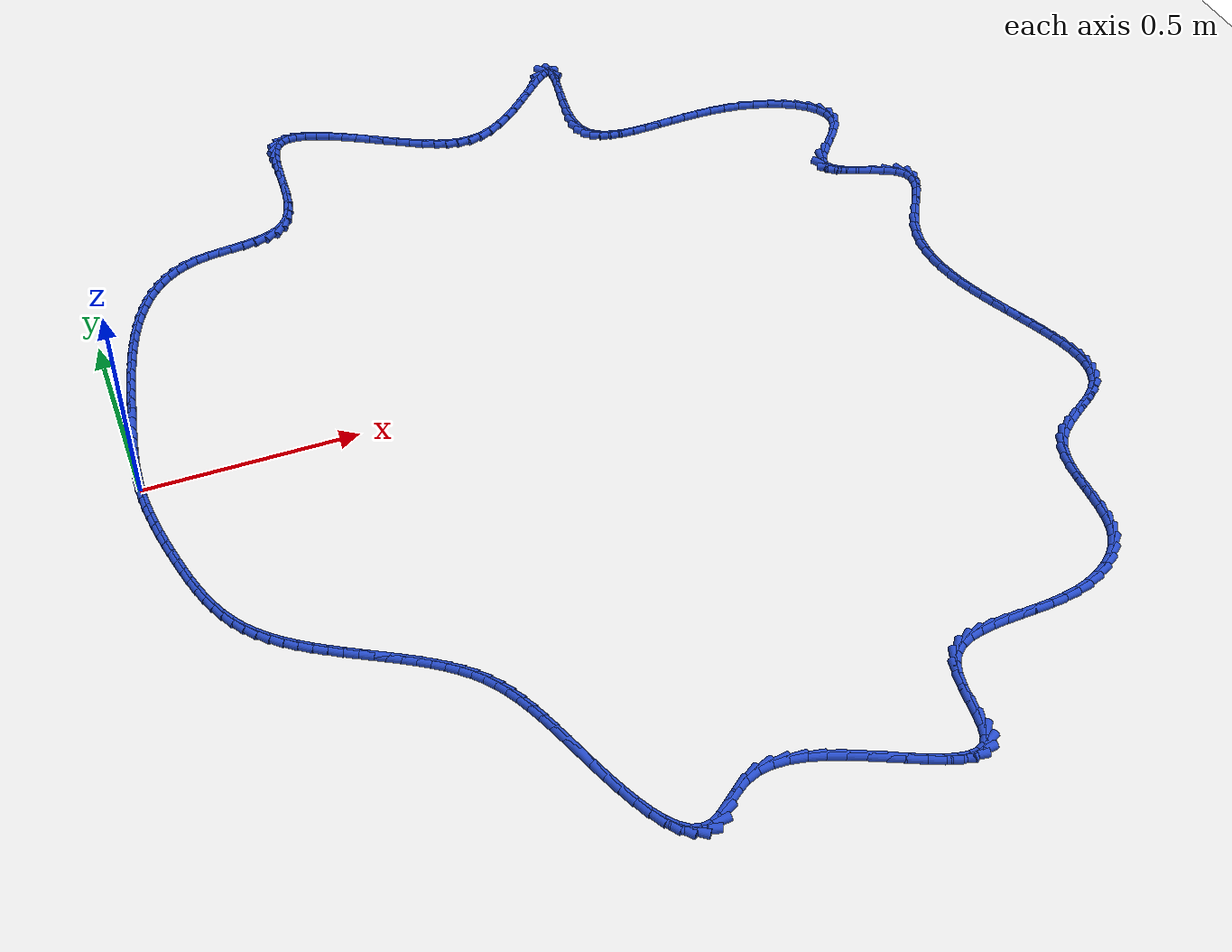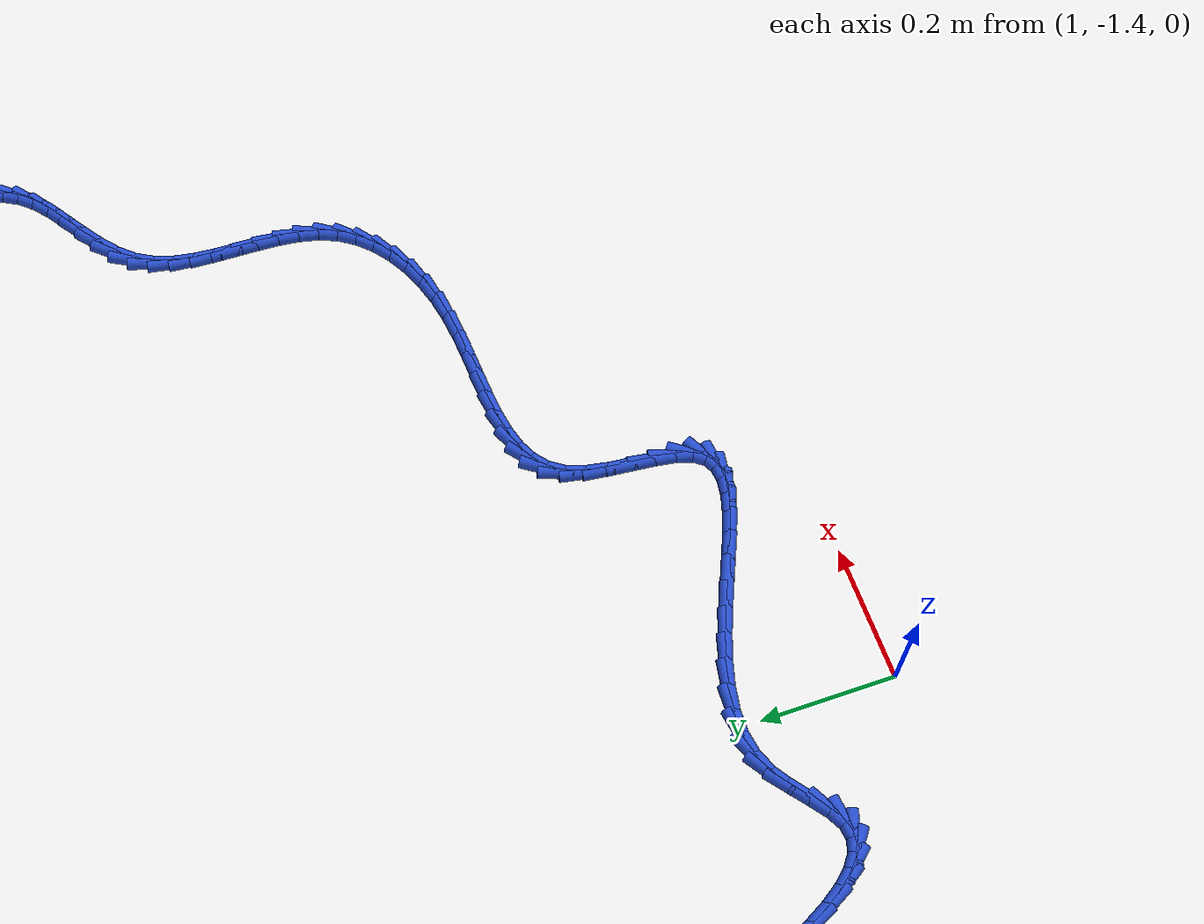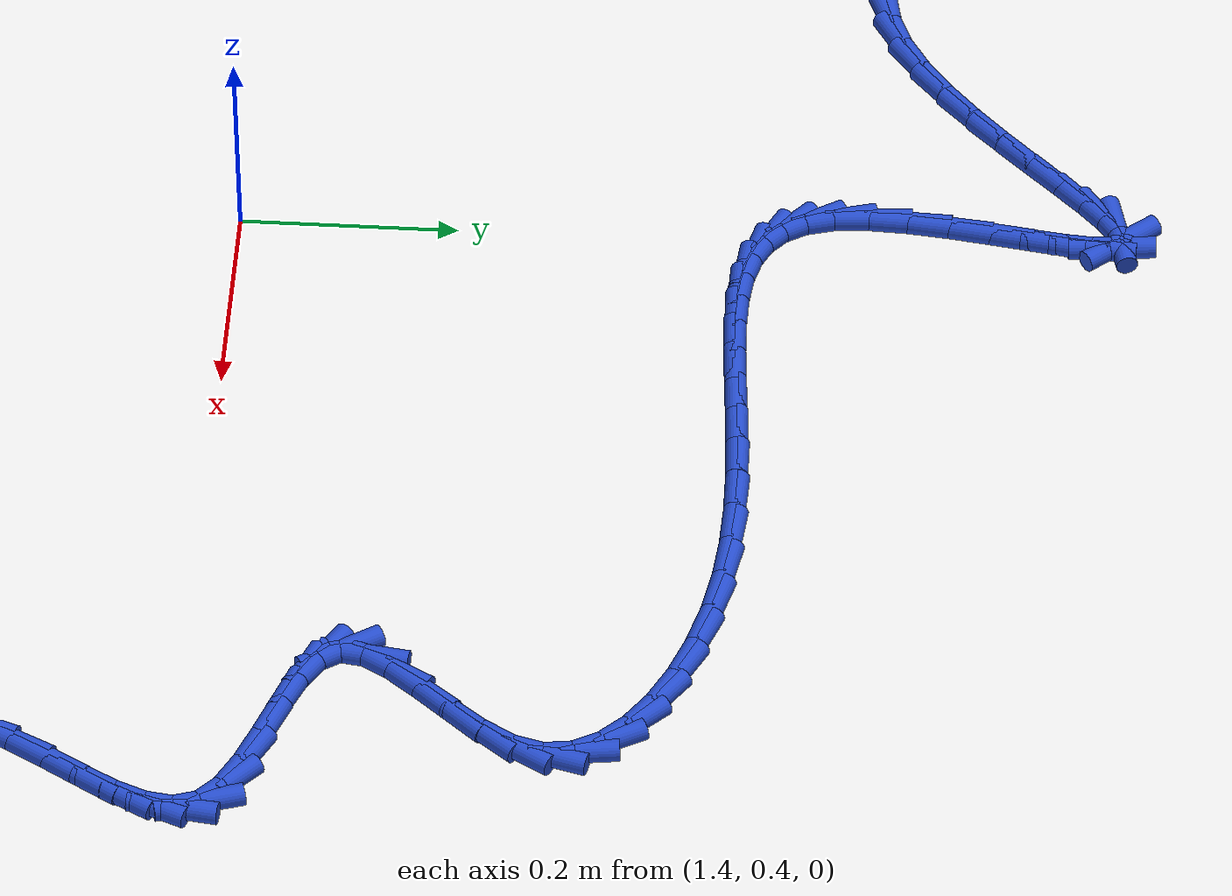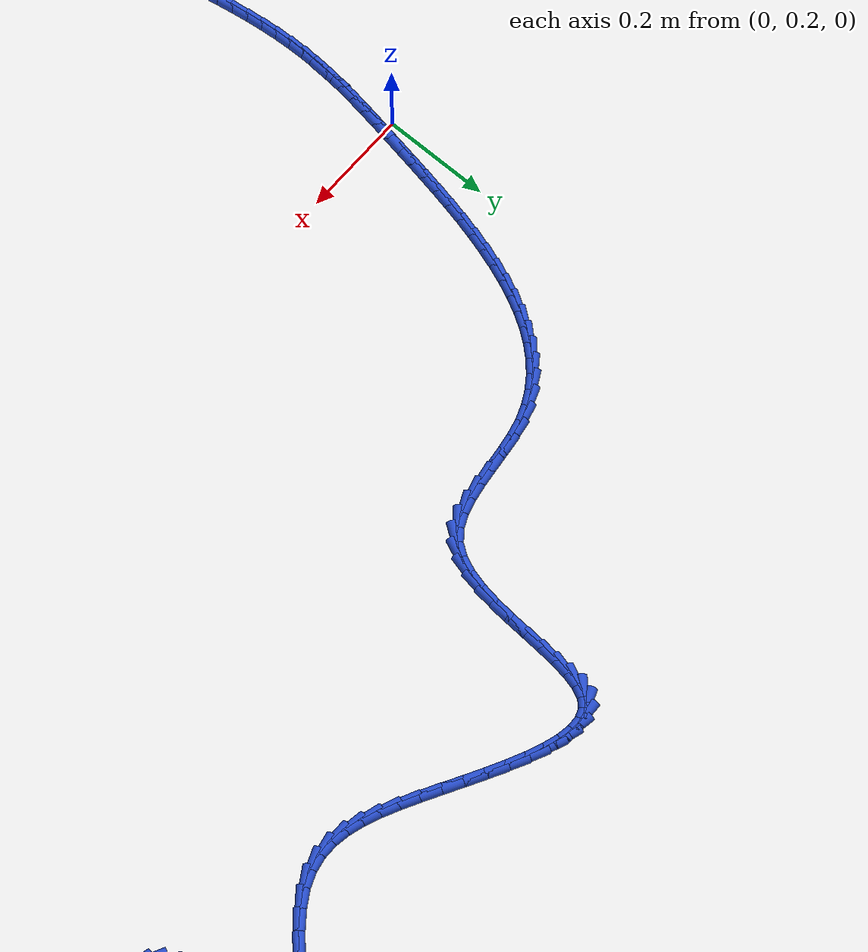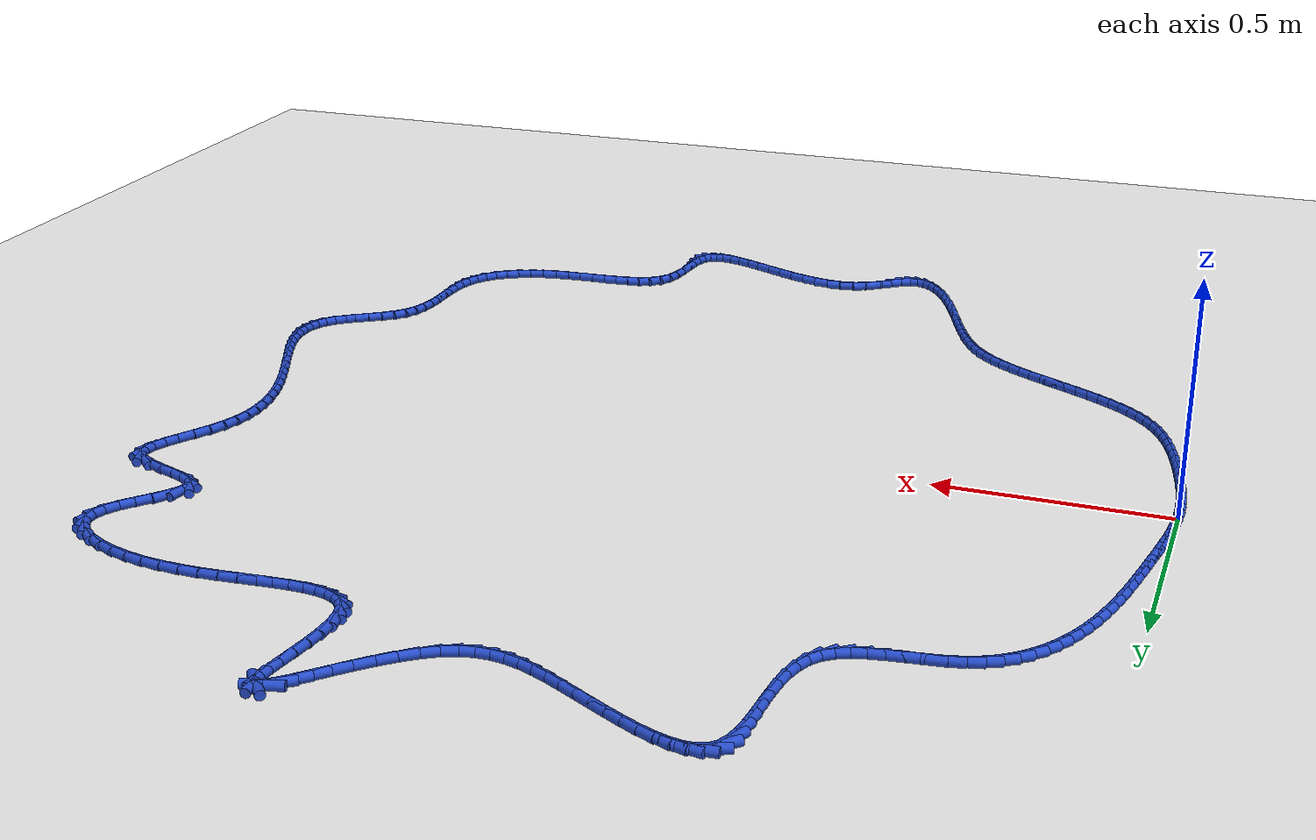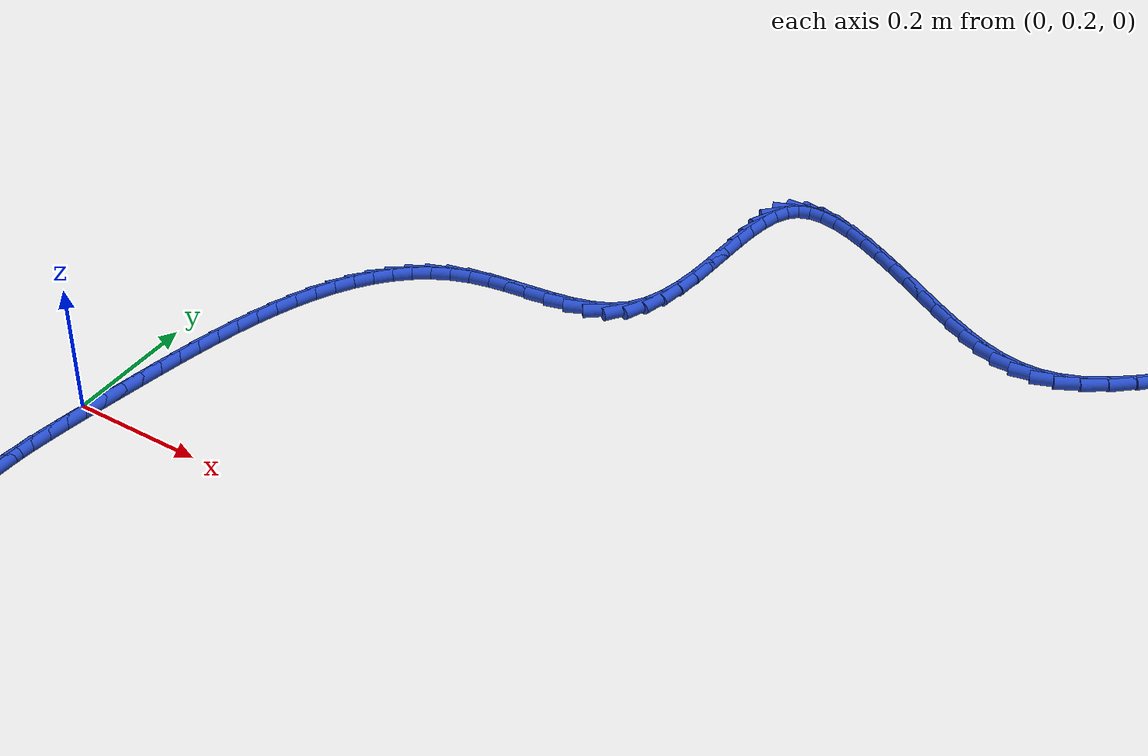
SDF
<sdf version="1.6">
 <world name="default">
  <light name="sun" type="directional">
   <pose>0 0 10 0 -0 0</pose>
   <diffuse>0.8 0.8 0.8 1</diffuse>
   <specular>0.2 0.2 0.2 1</specular>
   <attenuation>
    <range>1000</range>
    <constant>0.9</constant>
    <linear>0.01</linear>
    <quadratic>0.001</quadratic>
   </attenuation>
   <direction>-0.5 0.1 -0.9</direction>
  </light>
  <model name="ground_plane">
   <static>1</static>
   <link name="link">
    <collision name="collision">
     <geometry><plane><normal>0 0 1</normal><size>100 100</size></plane></geometry>
     <surface><friction><ode><mu>100</mu><mu2>50</mu2></ode></friction></surface>
    </collision>
    <visual name="visual">
     <cast_shadows>0</cast_shadows>
     <geometry><plane><normal>0 0 1</normal><size>100 100</size></plane></geometry>
     <material>
      <script><uri>file://media/materials/scripts/gazebo.material</uri><name>Gazebo/WhiteGlow</name></script>
     </material>
    </visual>
   </link>
  </model>
  <gravity>0 0 -9.8</gravity>
  <magnetic_field>6e-06 2.3e-05 -4.2e-05</magnetic_field>
  <atmosphere type="adiabatic"/>
  <physics name="default_physics" default="0" type="ode">
   <max_step_size>0.001</max_step_size>
   <real_time_factor>1</real_time_factor>
   <real_time_update_rate>1000</real_time_update_rate>
  </physics>
  <scene><ambient>0.4 0.4 0.4 1</ambient><background>0.7 0.7 0.7 1</background><shadows>1</shadows></scene>
  <spherical_coordinates>
   <surface_model>EARTH_WGS84</surface_model>
   <latitude_deg>0</latitude_deg>
   <longitude_deg>0</longitude_deg>
   <elevation>0</elevation>
   <heading_deg>0</heading_deg>
  </spherical_coordinates>
  <model name="line">
   <link name="link_0">
    <pose>-2.3418766925686896e-17 2.7755575615628914e-17 0.01 0 1.57 1.5431840335242455</pose>
    <collision name="collision">
     <geometry><cylinder><radius>0.01</radius><length>0.08</length></cylinder></geometry>
    </collision>
    <visual name="visual">
     <material>
      <script><name>Gazebo/Blue</name><uri>file://media/materials/scripts/gazebo.material</uri></script>
     </material>
     <geometry><cylinder><radius>0.01</radius><length>0.08</length></cylinder></geometry>
    </visual>
   </link>
   <link name="link_1">
    <pose>0.0008205790836752634 0.029710336549701805 0.01 0 1.57 1.50552651921383</pose>
    <collision name="collision">
     <geometry><cylinder><radius>0.01</radius><length>0.08</length></cylinder></geometry>
    </collision>
    <visual name="visual">
     <material>
      <script><name>Gazebo/Blue</name><uri>file://media/materials/scripts/gazebo.material</uri></script>
     </material>
     <geometry><cylinder><radius>0.01</radius><length>0.08</length></cylinder></geometry>
    </visual>
   </link>
   <link name="link_2">
    <pose>0.0027581841918830462 0.05935425467118082 0.01 0 1.57 1.473147145253619</pose>
    <collision name="collision">
     <geometry><cylinder><radius>0.01</radius><length>0.08</length></cylinder></geometry>
    </collision>
    <visual name="visual">
     <material>
      <script><name>Gazebo/Blue</name><uri>file://media/materials/scripts/gazebo.material</uri></script>
     </material>
     <geometry><cylinder><radius>0.01</radius><length>0.08</length></cylinder></geometry>
    </visual>
   </link>
   <link name="link_3">
    <pose>0.005669025520075664 0.08906862011442201 0.01 0 1.57 1.4464387678759532</pose>
    <collision name="collision">
     <geometry><cylinder><radius>0.01</radius><length>0.08</length></cylinder></geometry>
    </collision>
    <visual name="visual">
     <material>
      <script><name>Gazebo/Blue</name><uri>file://media/materials/scripts/gazebo.material</uri></script>
     </material>
     <geometry><cylinder><radius>0.01</radius><length>0.08</length></cylinder></geometry>
    </visual>
   </link>
   <link name="link_4">
    <pose>0.00940931326370546 0.11899029862941032 0.01 0 1.57 1.4255900085189623</pose>
    <collision name="collision">
     <geometry><cylinder><radius>0.01</radius><length>0.08</length></cylinder></geometry>
    </collision>
    <visual name="visual">
     <material>
      <script><name>Gazebo/Blue</name><uri>file://media/materials/scripts/gazebo.material</uri></script>
     </material>
     <geometry><cylinder><radius>0.01</radius><length>0.08</length></cylinder></geometry>
    </visual>
   </link>
   <link name="link_5">
    <pose>0.013835257618224761 0.14925615596613062 0.01 0 1.57 1.4106095447927667</pose>
    <collision name="collision">
     <geometry><cylinder><radius>0.01</radius><length>0.08</length></cylinder></geometry>
    </collision>
    <visual name="visual">
     <material>
      <script><name>Gazebo/Blue</name><uri>file://media/materials/scripts/gazebo.material</uri></script>
     </material>
     <geometry><cylinder><radius>0.01</radius><length>0.08</length></cylinder></geometry>
    </visual>
   </link>
   <link name="link_6">
    <pose>0.018803068779085916 0.18000305787456794 0.01 0 1.57 1.4013568138451076</pose>
    <collision name="collision">
     <geometry><cylinder><radius>0.01</radius><length>0.08</length></cylinder></geometry>
    </collision>
    <visual name="visual">
     <material>
      <script><name>Gazebo/Blue</name><uri>file://media/materials/scripts/gazebo.material</uri></script>
     </material>
     <geometry><cylinder><radius>0.01</radius><length>0.08</length></cylinder></geometry>
    </visual>
   </link>
   <link name="link_7">
    <pose>0.02416895694174127 0.21136787010470726 0.01 0 1.57 1.397569741843321</pose>
    <collision name="collision">
     <geometry><cylinder><radius>0.01</radius><length>0.08</length></cylinder></geometry>
    </collision>
    <visual name="visual">
     <material>
      <script><name>Gazebo/Blue</name><uri>file://media/materials/scripts/gazebo.material</uri></script>
     </material>
     <geometry><cylinder><radius>0.01</radius><length>0.08</length></cylinder></geometry>
    </visual>
   </link>
   <link name="link_8">
    <pose>0.029789229954243227 0.24348732534745177 0.01 0 1.57 1.396500510977313</pose>
    <collision name="collision">
     <geometry><cylinder><radius>0.01</radius><length>0.08</length></cylinder></geometry>
    </collision>
    <visual name="visual">
     <material>
      <script><name>Gazebo/Blue</name><uri>file://media/materials/scripts/gazebo.material</uri></script>
     </material>
     <geometry><cylinder><radius>0.01</radius><length>0.08</length></cylinder></geometry>
    </visual>
   </link>
   <link name="link_9">
    <pose>0.03558605786783621 0.27640841404143074 0.01 0 1.57 1.3915085409926655</pose>
    <collision name="collision">
     <geometry><cylinder><radius>0.01</radius><length>0.08</length></cylinder></geometry>
    </collision>
    <visual name="visual">
     <material>
      <script><name>Gazebo/Blue</name><uri>file://media/materials/scripts/gazebo.material</uri></script>
     </material>
     <geometry><cylinder><radius>0.01</radius><length>0.08</length></cylinder></geometry>
    </visual>
   </link>
   <link name="link_10">
    <pose>0.04166178018431136 0.309932632069983 0.01 0 1.57 1.3816417532952412</pose>
    <collision name="collision">
     <geometry><cylinder><radius>0.01</radius><length>0.08</length></cylinder></geometry>
    </collision>
    <visual name="visual">
     <material>
      <script><name>Gazebo/Blue</name><uri>file://media/materials/scripts/gazebo.material</uri></script>
     </material>
     <geometry><cylinder><radius>0.01</radius><length>0.08</length></cylinder></geometry>
    </visual>
   </link>
   <link name="link_11">
    <pose>0.048149265617327096 0.3438198769474235 0.01 0 1.57 1.3669043718705038</pose>
    <collision name="collision">
     <geometry><cylinder><radius>0.01</radius><length>0.08</length></cylinder></geometry>
    </collision>
    <visual name="visual">
     <material>
      <script><name>Gazebo/Blue</name><uri>file://media/materials/scripts/gazebo.material</uri></script>
     </material>
     <geometry><cylinder><radius>0.01</radius><length>0.08</length></cylinder></geometry>
    </visual>
   </link>
   <link name="link_12">
    <pose>0.055181382880541786 0.37783004618806704 0.01 0 1.57 1.347132735977017</pose>
    <collision name="collision">
     <geometry><cylinder><radius>0.01</radius><length>0.08</length></cylinder></geometry>
    </collision>
    <visual name="visual">
     <material>
      <script><name>Gazebo/Blue</name><uri>file://media/materials/scripts/gazebo.material</uri></script>
     </material>
     <geometry><cylinder><radius>0.01</radius><length>0.08</length></cylinder></geometry>
    </visual>
   </link>
   <link name="link_13">
    <pose>0.06289100068761386 0.41172303730622845 0.01 0 1.57 1.3220028289862888</pose>
    <collision name="collision">
     <geometry><cylinder><radius>0.01</radius><length>0.08</length></cylinder></geometry>
    </collision>
    <visual name="visual">
     <material>
      <script><name>Gazebo/Blue</name><uri>file://media/materials/scripts/gazebo.material</uri></script>
     </material>
     <geometry><cylinder><radius>0.01</radius><length>0.08</length></cylinder></geometry>
    </visual>
   </link>
   <link name="link_14">
    <pose>0.07141098775220173 0.4452587478162229 0.01 0 1.57 1.2910300230309852</pose>
    <collision name="collision">
     <geometry><cylinder><radius>0.01</radius><length>0.08</length></cylinder></geometry>
    </collision>
    <visual name="visual">
     <material>
      <script><name>Gazebo/Blue</name><uri>file://media/materials/scripts/gazebo.material</uri></script>
     </material>
     <geometry><cylinder><radius>0.01</radius><length>0.08</length></cylinder></geometry>
    </visual>
   </link>
   <link name="link_15">
    <pose>0.08087421278796372 0.47819707523236465 0.01 0 1.57 1.253565006715181</pose>
    <collision name="collision">
     <geometry><cylinder><radius>0.01</radius><length>0.08</length></cylinder></geometry>
    </collision>
    <visual name="visual">
     <material>
      <script><name>Gazebo/Blue</name><uri>file://media/materials/scripts/gazebo.material</uri></script>
     </material>
     <geometry><cylinder><radius>0.01</radius><length>0.08</length></cylinder></geometry>
    </visual>
   </link>
   <link name="link_16">
    <pose>0.09141354450855828 0.5102979170689689 0.01 0 1.57 1.208791385753163</pose>
    <collision name="collision">
     <geometry><cylinder><radius>0.01</radius><length>0.08</length></cylinder></geometry>
    </collision>
    <visual name="visual">
     <material>
      <script><name>Gazebo/Blue</name><uri>file://media/materials/scripts/gazebo.material</uri></script>
     </material>
     <geometry><cylinder><radius>0.01</radius><length>0.08</length></cylinder></geometry>
    </visual>
   </link>
   <link name="link_17">
    <pose>0.10316185162764382 0.5413211708403504 0.01 0 1.57 1.1557338823651864</pose>
    <collision name="collision">
     <geometry><cylinder><radius>0.01</radius><length>0.08</length></cylinder></geometry>
    </collision>
    <visual name="visual">
     <material>
      <script><name>Gazebo/Blue</name><uri>file://media/materials/scripts/gazebo.material</uri></script>
     </material>
     <geometry><cylinder><radius>0.01</radius><length>0.08</length></cylinder></geometry>
    </visual>
   </link>
   <link name="link_18">
    <pose>0.1162520028588787 0.5710267340608242 0.01 0 1.57 1.0932919653676183</pose>
    <collision name="collision">
     <geometry><cylinder><radius>0.01</radius><length>0.08</length></cylinder></geometry>
    </collision>
    <visual name="visual">
     <material>
      <script><name>Gazebo/Blue</name><uri>file://media/materials/scripts/gazebo.material</uri></script>
     </material>
     <geometry><cylinder><radius>0.01</radius><length>0.08</length></cylinder></geometry>
    </visual>
   </link>
   <link name="link_19">
    <pose>0.13081686691592137 0.599174504244705 0.01 0 1.57 1.020322042075308</pose>
    <collision name="collision">
     <geometry><cylinder><radius>0.01</radius><length>0.08</length></cylinder></geometry>
    </collision>
    <visual name="visual">
     <material>
      <script><name>Gazebo/Blue</name><uri>file://media/materials/scripts/gazebo.material</uri></script>
     </material>
     <geometry><cylinder><radius>0.01</radius><length>0.08</length></cylinder></geometry>
    </visual>
   </link>
   <link name="link_20">
    <pose>0.14698931251243016 0.6255243789063073 0.01 0 1.57 0.9357994101545254</pose>
    <collision name="collision">
     <geometry><cylinder><radius>0.01</radius><length>0.08</length></cylinder></geometry>
    </collision>
    <visual name="visual">
     <material>
      <script><name>Gazebo/Blue</name><uri>file://media/materials/scripts/gazebo.material</uri></script>
     </material>
     <geometry><cylinder><radius>0.01</radius><length>0.08</length></cylinder></geometry>
    </visual>
   </link>
   <link name="link_21">
    <pose>0.16490220836206354 0.6498362555599466 0.01 0 1.57 0.8390902157389397</pose>
    <collision name="collision">
     <geometry><cylinder><radius>0.01</radius><length>0.08</length></cylinder></geometry>
    </collision>
    <visual name="visual">
     <material>
      <script><name>Gazebo/Blue</name><uri>file://media/materials/scripts/gazebo.material</uri></script>
     </material>
     <geometry><cylinder><radius>0.01</radius><length>0.08</length></cylinder></geometry>
    </visual>
   </link>
   <link name="link_22">
    <pose>0.1846884231784799 0.6718700317199374 0.01 0 1.57 0.7303354842152526</pose>
    <collision name="collision">
     <geometry><cylinder><radius>0.01</radius><length>0.08</length></cylinder></geometry>
    </collision>
    <visual name="visual">
     <material>
      <script><name>Gazebo/Blue</name><uri>file://media/materials/scripts/gazebo.material</uri></script>
     </material>
     <geometry><cylinder><radius>0.01</radius><length>0.08</length></cylinder></geometry>
    </visual>
   </link>
   <link name="link_23">
    <pose>0.20648082567533757 0.6913856049005946 0.01 0 1.57 0.610873083414487</pose>
    <collision name="collision">
     <geometry><cylinder><radius>0.01</radius><length>0.08</length></cylinder></geometry>
    </collision>
    <visual name="visual">
     <material>
      <script><name>Gazebo/Blue</name><uri>file://media/materials/scripts/gazebo.material</uri></script>
     </material>
     <geometry><cylinder><radius>0.01</radius><length>0.08</length></cylinder></geometry>
    </visual>
   </link>
   <link name="link_24">
    <pose>0.23041228456629503 0.7081428726162331 0.01 0 1.57 0.4835093218167435</pose>
    <collision name="collision">
     <geometry><cylinder><radius>0.01</radius><length>0.08</length></cylinder></geometry>
    </collision>
    <visual name="visual">
     <material>
      <script><name>Gazebo/Blue</name><uri>file://media/materials/scripts/gazebo.material</uri></script>
     </material>
     <geometry><cylinder><radius>0.01</radius><length>0.08</length></cylinder></geometry>
    </visual>
   </link>
   <link name="link_25">
    <pose>0.25661566856501056 0.7219017323811675 0.01 0 1.57 0.35238991997093994</pose>
    <collision name="collision">
     <geometry><cylinder><radius>0.01</radius><length>0.08</length></cylinder></geometry>
    </collision>
    <visual name="visual">
     <material>
      <script><name>Gazebo/Blue</name><uri>file://media/materials/scripts/gazebo.material</uri></script>
     </material>
     <geometry><cylinder><radius>0.01</radius><length>0.08</length></cylinder></geometry>
    </visual>
   </link>
   <link name="link_26">
    <pose>0.28522384638514275 0.7324220817097131 0.01 0 1.57 0.2298701826235086</pose>
    <collision name="collision">
     <geometry><cylinder><radius>0.01</radius><length>0.08</length></cylinder></geometry>
    </collision>
    <visual name="visual">
     <material>
      <script><name>Gazebo/Blue</name><uri>file://media/materials/scripts/gazebo.material</uri></script>
     </material>
     <geometry><cylinder><radius>0.01</radius><length>0.08</length></cylinder></geometry>
    </visual>
   </link>
   <link name="link_27">
    <pose>0.3162094445750726 0.7396729109899698 0.01 0 1.57 0.1501688839219765</pose>
    <collision name="collision">
     <geometry><cylinder><radius>0.01</radius><length>0.08</length></cylinder></geometry>
    </collision>
    <visual name="visual">
     <material>
      <script><name>Gazebo/Blue</name><uri>file://media/materials/scripts/gazebo.material</uri></script>
     </material>
     <geometry><cylinder><radius>0.01</radius><length>0.08</length></cylinder></geometry>
    </visual>
   </link>
   <link name="link_28">
    <pose>0.3487940414781982 0.7446032200055676 0.01 0 1.57 0.11536979349667276</pose>
    <collision name="collision">
     <geometry><cylinder><radius>0.01</radius><length>0.08</length></cylinder></geometry>
    </collision>
    <visual name="visual">
     <material>
      <script><name>Gazebo/Blue</name><uri>file://media/materials/scripts/gazebo.material</uri></script>
     </material>
     <geometry><cylinder><radius>0.01</radius><length>0.08</length></cylinder></geometry>
    </visual>
   </link>
   <link name="link_29">
    <pose>0.3819793652471812 0.7484488812749355 0.01 0 1.57 0.12130439466043336</pose>
    <collision name="collision">
     <geometry><cylinder><radius>0.01</radius><length>0.08</length></cylinder></geometry>
    </collision>
    <visual name="visual">
     <material>
      <script><name>Gazebo/Blue</name><uri>file://media/materials/scripts/gazebo.material</uri></script>
     </material>
     <geometry><cylinder><radius>0.01</radius><length>0.08</length></cylinder></geometry>
    </visual>
   </link>
   <link name="link_30">
    <pose>0.4147671163705326 0.752445803414223 0.01 0 1.57 0.16985955729170202</pose>
    <collision name="collision">
     <geometry><cylinder><radius>0.01</radius><length>0.08</length></cylinder></geometry>
    </collision>
    <visual name="visual">
     <material>
      <script><name>Gazebo/Blue</name><uri>file://media/materials/scripts/gazebo.material</uri></script>
     </material>
     <geometry><cylinder><radius>0.01</radius><length>0.08</length></cylinder></geometry>
    </visual>
   </link>
   <link name="link_31">
    <pose>0.44615899533676384 0.7578298950395792 0.01 0 1.57 0.26941751046165724</pose>
    <collision name="collision">
     <geometry><cylinder><radius>0.01</radius><length>0.08</length></cylinder></geometry>
    </collision>
    <visual name="visual">
     <material>
      <script><name>Gazebo/Blue</name><uri>file://media/materials/scripts/gazebo.material</uri></script>
     </material>
     <geometry><cylinder><radius>0.01</radius><length>0.08</length></cylinder></geometry>
    </visual>
   </link>
   <link name="link_32">
    <pose>0.4751567026343858 0.7658370647671527 0.01 0 1.57 0.4339635068815142</pose>
    <collision name="collision">
     <geometry><cylinder><radius>0.01</radius><length>0.08</length></cylinder></geometry>
    </collision>
    <visual name="visual">
     <material>
      <script><name>Gazebo/Blue</name><uri>file://media/materials/scripts/gazebo.material</uri></script>
     </material>
     <geometry><cylinder><radius>0.01</radius><length>0.08</length></cylinder></geometry>
    </visual>
   </link>
   <link name="link_33">
    <pose>0.5007619387519098 0.777703221213093 0.01 0 1.57 0.674437882276421</pose>
    <collision name="collision">
     <geometry><cylinder><radius>0.01</radius><length>0.08</length></cylinder></geometry>
    </collision>
    <visual name="visual">
     <material>
      <script><name>Gazebo/Blue</name><uri>file://media/materials/scripts/gazebo.material</uri></script>
     </material>
     <geometry><cylinder><radius>0.01</radius><length>0.08</length></cylinder></geometry>
    </visual>
   </link>
   <link name="link_34">
    <pose>0.5219764141205137 0.7946642600806357 0.01 0 1.57 0.9550952539210807</pose>
    <collision name="collision">
     <geometry><cylinder><radius>0.01</radius><length>0.08</length></cylinder></geometry>
    </collision>
    <visual name="visual">
     <material>
      <script><name>Gazebo/Blue</name><uri>file://media/materials/scripts/gazebo.material</uri></script>
     </material>
     <geometry><cylinder><radius>0.01</radius><length>0.08</length></cylinder></geometry>
    </visual>
   </link>
   <link name="link_35">
    <pose>0.5381416971866676 0.817514690746872 0.01 0 1.57 1.1742861780606355</pose>
    <collision name="collision">
     <geometry><cylinder><radius>0.01</radius><length>0.08</length></cylinder></geometry>
    </collision>
    <visual name="visual">
     <material>
      <script><name>Gazebo/Blue</name><uri>file://media/materials/scripts/gazebo.material</uri></script>
     </material>
     <geometry><cylinder><radius>0.01</radius><length>0.08</length></cylinder></geometry>
    </visual>
   </link>
   <link name="link_36">
    <pose>0.5498352587173954 0.8454439099824648 0.01 0 1.57 1.3222137875140283</pose>
    <collision name="collision">
     <geometry><cylinder><radius>0.01</radius><length>0.08</length></cylinder></geometry>
    </collision>
    <visual name="visual">
     <material>
      <script><name>Gazebo/Blue</name><uri>file://media/materials/scripts/gazebo.material</uri></script>
     </material>
     <geometry><cylinder><radius>0.01</radius><length>0.08</length></cylinder></geometry>
    </visual>
   </link>
   <link name="link_37">
    <pose>0.5579154226606409 0.8772765600190204 0.01 0 1.57 1.417919299343995</pose>
    <collision name="collision">
     <geometry><cylinder><radius>0.01</radius><length>0.08</length></cylinder></geometry>
    </collision>
    <visual name="visual">
     <material>
      <script><name>Gazebo/Blue</name><uri>file://media/materials/scripts/gazebo.material</uri></script>
     </material>
     <geometry><cylinder><radius>0.01</radius><length>0.08</length></cylinder></geometry>
    </visual>
   </link>
   <link name="link_38">
    <pose>0.563240512964348 0.911837283088146 0.01 0 1.57 1.4761474328278965</pose>
    <collision name="collision">
     <geometry><cylinder><radius>0.01</radius><length>0.08</length></cylinder></geometry>
    </collision>
    <visual name="visual">
     <material>
      <script><name>Gazebo/Blue</name><uri>file://media/materials/scripts/gazebo.material</uri></script>
     </material>
     <geometry><cylinder><radius>0.01</radius><length>0.08</length></cylinder></geometry>
    </visual>
   </link>
   <link name="link_39">
    <pose>0.5666688535764606 0.947950721421449 0.01 0 1.57 1.5053960945276603</pose>
    <collision name="collision">
     <geometry><cylinder><radius>0.01</radius><length>0.08</length></cylinder></geometry>
    </collision>
    <visual name="visual">
     <material>
      <script><name>Gazebo/Blue</name><uri>file://media/materials/scripts/gazebo.material</uri></script>
     </material>
     <geometry><cylinder><radius>0.01</radius><length>0.08</length></cylinder></geometry>
    </visual>
   </link>
   <link name="link_40">
    <pose>0.5690587684449228 0.9844415172505356 0.01 0 1.57 1.5089632303011677</pose>
    <collision name="collision">
     <geometry><cylinder><radius>0.01</radius><length>0.08</length></cylinder></geometry>
    </collision>
    <visual name="visual">
     <material>
      <script><name>Gazebo/Blue</name><uri>file://media/materials/scripts/gazebo.material</uri></script>
     </material>
     <geometry><cylinder><radius>0.01</radius><length>0.08</length></cylinder></geometry>
    </visual>
   </link>
   <link name="link_41">
    <pose>0.5712685815176783 1.0201343128070128 0.01 0 1.57 1.4853558689104662</pose>
    <collision name="collision">
     <geometry><cylinder><radius>0.01</radius><length>0.08</length></cylinder></geometry>
    </collision>
    <visual name="visual">
     <material>
      <script><name>Gazebo/Blue</name><uri>file://media/materials/scripts/gazebo.material</uri></script>
     </material>
     <geometry><cylinder><radius>0.01</radius><length>0.08</length></cylinder></geometry>
    </visual>
   </link>
   <link name="link_42">
    <pose>0.5741566167426714 1.053853750322488 0.01 0 1.57 1.4270617674186972</pose>
    <collision name="collision">
     <geometry><cylinder><radius>0.01</radius><length>0.08</length></cylinder></geometry>
    </collision>
    <visual name="visual">
     <material>
      <script><name>Gazebo/Blue</name><uri>file://media/materials/scripts/gazebo.material</uri></script>
     </material>
     <geometry><cylinder><radius>0.01</radius><length>0.08</length></cylinder></geometry>
    </visual>
   </link>
   <link name="link_43">
    <pose>0.578581198067846 1.0844244720285683 0.01 0 1.57 1.3165951914812444</pose>
    <collision name="collision">
     <geometry><cylinder><radius>0.01</radius><length>0.08</length></cylinder></geometry>
    </collision>
    <visual name="visual">
     <material>
      <script><name>Gazebo/Blue</name><uri>file://media/materials/scripts/gazebo.material</uri></script>
     </material>
     <geometry><cylinder><radius>0.01</radius><length>0.08</length></cylinder></geometry>
    </visual>
   </link>
   <link name="link_44">
    <pose>0.5854006494411456 1.110671120156859 0.01 0 1.57 1.1188208683266396</pose>
    <collision name="collision">
     <geometry><cylinder><radius>0.01</radius><length>0.08</length></cylinder></geometry>
    </collision>
    <visual name="visual">
     <material>
      <script><name>Gazebo/Blue</name><uri>file://media/materials/scripts/gazebo.material</uri></script>
     </material>
     <geometry><cylinder><radius>0.01</radius><length>0.08</length></cylinder></geometry>
    </visual>
   </link>
   <link name="link_45">
    <pose>0.5954732948105146 1.1314183369389692 0.01 0 1.57 0.7827034766472749</pose>
    <collision name="collision">
     <geometry><cylinder><radius>0.01</radius><length>0.08</length></cylinder></geometry>
    </collision>
    <visual name="visual">
     <material>
      <script><name>Gazebo/Blue</name><uri>file://media/materials/scripts/gazebo.material</uri></script>
     </material>
     <geometry><cylinder><radius>0.01</radius><length>0.08</length></cylinder></geometry>
    </visual>
   </link>
   <link name="link_46">
    <pose>0.6096428105415517 1.1455116928997957 0.01 0 1.57 0.36665389753765604</pose>
    <collision name="collision">
     <geometry><cylinder><radius>0.01</radius><length>0.08</length></cylinder></geometry>
    </collision>
    <visual name="visual">
     <material>
      <script><name>Gazebo/Blue</name><uri>file://media/materials/scripts/gazebo.material</uri></script>
     </material>
     <geometry><cylinder><radius>0.01</radius><length>0.08</length></cylinder></geometry>
    </visual>
   </link>
   <link name="link_47">
    <pose>0.6281716997895691 1.1526271320082226 0.01 0 1.57 0.040264353662635054</pose>
    <collision name="collision">
     <geometry><cylinder><radius>0.01</radius><length>0.08</length></cylinder></geometry>
    </collision>
    <visual name="visual">
     <material>
      <script><name>Gazebo/Blue</name><uri>file://media/materials/scripts/gazebo.material</uri></script>
     </material>
     <geometry><cylinder><radius>0.01</radius><length>0.08</length></cylinder></geometry>
    </visual>
   </link>
   <link name="link_48">
    <pose>0.6505606332940201 1.1535290954241595 0.01 0 1.57 -0.17234588412058333</pose>
    <collision name="collision">
     <geometry><cylinder><radius>0.01</radius><length>0.08</length></cylinder></geometry>
    </collision>
    <visual name="visual">
     <material>
      <script><name>Gazebo/Blue</name><uri>file://media/materials/scripts/gazebo.material</uri></script>
     </material>
     <geometry><cylinder><radius>0.01</radius><length>0.08</length></cylinder></geometry>
    </visual>
   </link>
   <link name="link_49">
    <pose>0.6762586704834133 1.1490557659412661 0.01 0 1.57 -0.30665426514661104</pose>
    <collision name="collision">
     <geometry><cylinder><radius>0.01</radius><length>0.08</length></cylinder></geometry>
    </collision>
    <visual name="visual">
     <material>
      <script><name>Gazebo/Blue</name><uri>file://media/materials/scripts/gazebo.material</uri></script>
     </material>
     <geometry><cylinder><radius>0.01</radius><length>0.08</length></cylinder></geometry>
    </visual>
   </link>
   <link name="link_50">
    <pose>0.7047148707862567 1.140045326353201 0.01 0 1.57 -0.39292623963590634</pose>
    <collision name="collision">
     <geometry><cylinder><radius>0.01</radius><length>0.08</length></cylinder></geometry>
    </collision>
    <visual name="visual">
     <material>
      <script><name>Gazebo/Blue</name><uri>file://media/materials/scripts/gazebo.material</uri></script>
     </material>
     <geometry><cylinder><radius>0.01</radius><length>0.08</length></cylinder></geometry>
    </visual>
   </link>
   <link name="link_51">
    <pose>0.7353782936310586 1.1273359594536236 0.01 0 1.57 -0.44894365665205005</pose>
    <collision name="collision">
     <geometry><cylinder><radius>0.01</radius><length>0.08</length></cylinder></geometry>
    </collision>
    <visual name="visual">
     <material>
      <script><name>Gazebo/Blue</name><uri>file://media/materials/scripts/gazebo.material</uri></script>
     </material>
     <geometry><cylinder><radius>0.01</radius><length>0.08</length></cylinder></geometry>
    </visual>
   </link>
   <link name="link_52">
    <pose>0.7676979984463269 1.111765848036194 0.01 0 1.57 -0.48449066333439234</pose>
    <collision name="collision">
     <geometry><cylinder><radius>0.01</radius><length>0.08</length></cylinder></geometry>
    </collision>
    <visual name="visual">
     <material>
      <script><name>Gazebo/Blue</name><uri>file://media/materials/scripts/gazebo.material</uri></script>
     </material>
     <geometry><cylinder><radius>0.01</radius><length>0.08</length></cylinder></geometry>
    </visual>
   </link>
   <link name="link_53">
    <pose>0.8011230446605704 1.0941731748945713 0.01 0 1.57 -0.5048373976185873</pose>
    <collision name="collision">
     <geometry><cylinder><radius>0.01</radius><length>0.08</length></cylinder></geometry>
    </collision>
    <visual name="visual">
     <material>
      <script><name>Gazebo/Blue</name><uri>file://media/materials/scripts/gazebo.material</uri></script>
     </material>
     <geometry><cylinder><radius>0.01</radius><length>0.08</length></cylinder></geometry>
    </visual>
   </link>
   <link name="link_54">
    <pose>0.8351024917022972 1.075396122822415 0.01 0 1.57 -0.5125652068610111</pose>
    <collision name="collision">
     <geometry><cylinder><radius>0.01</radius><length>0.08</length></cylinder></geometry>
    </collision>
    <visual name="visual">
     <material>
      <script><name>Gazebo/Blue</name><uri>file://media/materials/scripts/gazebo.material</uri></script>
     </material>
     <geometry><cylinder><radius>0.01</radius><length>0.08</length></cylinder></geometry>
    </visual>
   </link>
   <link name="link_55">
    <pose>0.8690853990000155 1.0562728746133838 0.01 0 1.57 -0.5083780034503285</pose>
    <collision name="collision">
     <geometry><cylinder><radius>0.01</radius><length>0.08</length></cylinder></geometry>
    </collision>
    <visual name="visual">
     <material>
      <script><name>Gazebo/Blue</name><uri>file://media/materials/scripts/gazebo.material</uri></script>
     </material>
     <geometry><cylinder><radius>0.01</radius><length>0.08</length></cylinder></geometry>
    </visual>
   </link>
   <link name="link_56">
    <pose>0.902520825982233 1.0376416130611377 0.01 0 1.57 -0.4909156597733868</pose>
    <collision name="collision">
     <geometry><cylinder><radius>0.01</radius><length>0.08</length></cylinder></geometry>
    </collision>
    <visual name="visual">
     <material>
      <script><name>Gazebo/Blue</name><uri>file://media/materials/scripts/gazebo.material</uri></script>
     </material>
     <geometry><cylinder><radius>0.01</radius><length>0.08</length></cylinder></geometry>
    </visual>
   </link>
   <link name="link_57">
    <pose>0.9348978218388884 1.020334007853938 0.01 0 1.57 -0.45312876559290505</pose>
    <collision name="collision">
     <geometry><cylinder><radius>0.01</radius><length>0.08</length></cylinder></geometry>
    </collision>
    <visual name="visual">
     <material>
      <script><name>Gazebo/Blue</name><uri>file://media/materials/scripts/gazebo.material</uri></script>
     </material>
     <geometry><cylinder><radius>0.01</radius><length>0.08</length></cylinder></geometry>
    </visual>
   </link>
   <link name="link_58">
    <pose>0.9661727804954329 1.0051056125590505 0.01 0 1.57 -0.388135024559466</pose>
    <collision name="collision">
     <geometry><cylinder><radius>0.01</radius><length>0.08</length></cylinder></geometry>
    </collision>
    <visual name="visual">
     <material>
      <script><name>Gazebo/Blue</name><uri>file://media/materials/scripts/gazebo.material</uri></script>
     </material>
     <geometry><cylinder><radius>0.01</radius><length>0.08</length></cylinder></geometry>
    </visual>
   </link>
   <link name="link_59">
    <pose>0.9966047826361238 0.9926626823560493 0.01 0 1.57 -0.2913361071750208</pose>
    <collision name="collision">
     <geometry><cylinder><radius>0.01</radius><length>0.08</length></cylinder></geometry>
    </collision>
    <visual name="visual">
     <material>
      <script><name>Gazebo/Blue</name><uri>file://media/materials/scripts/gazebo.material</uri></script>
     </material>
     <geometry><cylinder><radius>0.01</radius><length>0.08</length></cylinder></geometry>
    </visual>
   </link>
   <link name="link_60">
    <pose>1.0264580067338676 0.983710642151119 0.01 0 1.57 -0.15963037158794874</pose>
    <collision name="collision">
     <geometry><cylinder><radius>0.01</radius><length>0.08</length></cylinder></geometry>
    </collision>
    <visual name="visual">
     <material>
      <script><name>Gazebo/Blue</name><uri>file://media/materials/scripts/gazebo.material</uri></script>
     </material>
     <geometry><cylinder><radius>0.01</radius><length>0.08</length></cylinder></geometry>
    </visual>
   </link>
   <link name="link_61">
    <pose>1.0559966312615698 0.9789549168504443 0.01 0 1.57 0.004951584004449901</pose>
    <collision name="collision">
     <geometry><cylinder><radius>0.01</radius><length>0.08</length></cylinder></geometry>
    </collision>
    <visual name="visual">
     <material>
      <script><name>Gazebo/Blue</name><uri>file://media/materials/scripts/gazebo.material</uri></script>
     </material>
     <geometry><cylinder><radius>0.01</radius><length>0.08</length></cylinder></geometry>
    </visual>
   </link>
   <link name="link_62">
    <pose>1.0854848346921369 0.9791009313602099 0.01 0 1.57 0.19132765447091377</pose>
    <collision name="collision">
     <geometry><cylinder><radius>0.01</radius><length>0.08</length></cylinder></geometry>
    </collision>
    <visual name="visual">
     <material>
      <script><name>Gazebo/Blue</name><uri>file://media/materials/scripts/gazebo.material</uri></script>
     </material>
     <geometry><cylinder><radius>0.01</radius><length>0.08</length></cylinder></geometry>
    </visual>
   </link>
   <link name="link_63">
    <pose>1.1151867954984744 0.9848541105866003 0.01 0 1.57 0.3803181798895723</pose>
    <collision name="collision">
     <geometry><cylinder><radius>0.01</radius><length>0.08</length></cylinder></geometry>
    </collision>
    <visual name="visual">
     <material>
      <script><name>Gazebo/Blue</name><uri>file://media/materials/scripts/gazebo.material</uri></script>
     </material>
     <geometry><cylinder><radius>0.01</radius><length>0.08</length></cylinder></geometry>
    </visual>
   </link>
   <link name="link_64">
    <pose>1.1453665325737021 0.9969194174110169 0.01 0 1.57 0.5428441008434026</pose>
    <collision name="collision">
     <geometry><cylinder><radius>0.01</radius><length>0.08</length></cylinder></geometry>
    </collision>
    <visual name="visual">
     <material>
      <script><name>Gazebo/Blue</name><uri>file://media/materials/scripts/gazebo.material</uri></script>
     </material>
     <geometry><cylinder><radius>0.01</radius><length>0.08</length></cylinder></geometry>
    </visual>
   </link>
   <link name="link_65">
    <pose>1.1761016010668832 1.0154619539172671 0.01 0 1.57 0.6535325606691467</pose>
    <collision name="collision">
     <geometry><cylinder><radius>0.01</radius><length>0.08</length></cylinder></geometry>
    </collision>
    <visual name="visual">
     <material>
      <script><name>Gazebo/Blue</name><uri>file://media/materials/scripts/gazebo.material</uri></script>
     </material>
     <geometry><cylinder><radius>0.01</radius><length>0.08</length></cylinder></geometry>
    </visual>
   </link>
   <link name="link_66">
    <pose>1.2069231784694563 1.0390649174627036 0.01 0 1.57 0.7264530151013725</pose>
    <collision name="collision">
     <geometry><cylinder><radius>0.01</radius><length>0.08</length></cylinder></geometry>
    </collision>
    <visual name="visual">
     <material>
      <script><name>Gazebo/Blue</name><uri>file://media/materials/scripts/gazebo.material</uri></script>
     </material>
     <geometry><cylinder><radius>0.01</radius><length>0.08</length></cylinder></geometry>
    </visual>
   </link>
   <link name="link_67">
    <pose>1.2372628866293298 1.0660232660507316 0.01 0 1.57 0.7736406593499286</pose>
    <collision name="collision">
     <geometry><cylinder><radius>0.01</radius><length>0.08</length></cylinder></geometry>
    </collision>
    <visual name="visual">
     <material>
      <script><name>Gazebo/Blue</name><uri>file://media/materials/scripts/gazebo.material</uri></script>
     </material>
     <geometry><cylinder><radius>0.01</radius><length>0.08</length></cylinder></geometry>
    </visual>
   </link>
   <link name="link_68">
    <pose>1.2665523473944107 1.0946319576847547 0.01 0 1.57 0.8011044781243333</pose>
    <collision name="collision">
     <geometry><cylinder><radius>0.01</radius><length>0.08</length></cylinder></geometry>
    </collision>
    <visual name="visual">
     <material>
      <script><name>Gazebo/Blue</name><uri>file://media/materials/scripts/gazebo.material</uri></script>
     </material>
     <geometry><cylinder><radius>0.01</radius><length>0.08</length></cylinder></geometry>
    </visual>
   </link>
   <link name="link_69">
    <pose>1.294223182612607 1.1231859503681776 0.01 0 1.57 0.8104592556146465</pose>
    <collision name="collision">
     <geometry><cylinder><radius>0.01</radius><length>0.08</length></cylinder></geometry>
    </collision>
    <visual name="visual">
     <material>
      <script><name>Gazebo/Blue</name><uri>file://media/materials/scripts/gazebo.material</uri></script>
     </material>
     <geometry><cylinder><radius>0.01</radius><length>0.08</length></cylinder></geometry>
    </visual>
   </link>
   <link name="link_70">
    <pose>1.3197070141318266 1.1499802021044045 0.01 0 1.57 0.7984466257177439</pose>
    <collision name="collision">
     <geometry><cylinder><radius>0.01</radius><length>0.08</length></cylinder></geometry>
    </collision>
    <visual name="visual">
     <material>
      <script><name>Gazebo/Blue</name><uri>file://media/materials/scripts/gazebo.material</uri></script>
     </material>
     <geometry><cylinder><radius>0.01</radius><length>0.08</length></cylinder></geometry>
    </visual>
   </link>
   <link name="link_71">
    <pose>1.342435463799977 1.1733096708968396 0.01 0 1.57 0.7522659317770498</pose>
    <collision name="collision">
     <geometry><cylinder><radius>0.01</radius><length>0.08</length></cylinder></geometry>
    </collision>
    <visual name="visual">
     <material>
      <script><name>Gazebo/Blue</name><uri>file://media/materials/scripts/gazebo.material</uri></script>
     </material>
     <geometry><cylinder><radius>0.01</radius><length>0.08</length></cylinder></geometry>
    </visual>
   </link>
   <link name="link_72">
    <pose>1.361840153464966 1.191469314748888 0.01 0 1.57 0.6289194446462302</pose>
    <collision name="collision">
     <geometry><cylinder><radius>0.01</radius><length>0.08</length></cylinder></geometry>
    </collision>
    <visual name="visual">
     <material>
      <script><name>Gazebo/Blue</name><uri>file://media/materials/scripts/gazebo.material</uri></script>
     </material>
     <geometry><cylinder><radius>0.01</radius><length>0.08</length></cylinder></geometry>
    </visual>
   </link>
   <link name="link_73">
    <pose>1.3773527049747019 1.2027540916639532 0.01 0 1.57 0.2400213735099397</pose>
    <collision name="collision">
     <geometry><cylinder><radius>0.01</radius><length>0.08</length></cylinder></geometry>
    </collision>
    <visual name="visual">
     <material>
      <script><name>Gazebo/Blue</name><uri>file://media/materials/scripts/gazebo.material</uri></script>
     </material>
     <geometry><cylinder><radius>0.01</radius><length>0.08</length></cylinder></geometry>
    </visual>
   </link>
   <link name="link_74">
    <pose>1.3884047401770923 1.2054589596454406 0.01 0 1.57 -0.8916329751993161</pose>
    <collision name="collision">
     <geometry><cylinder><radius>0.01</radius><length>0.08</length></cylinder></geometry>
    </collision>
    <visual name="visual">
     <material>
      <script><name>Gazebo/Blue</name><uri>file://media/materials/scripts/gazebo.material</uri></script>
     </material>
     <geometry><cylinder><radius>0.01</radius><length>0.08</length></cylinder></geometry>
    </visual>
   </link>
   <link name="link_75">
    <pose>1.3944635298059607 1.1979537563542686 0.01 0 1.57 -1.4926427483449498</pose>
    <collision name="collision">
     <geometry><cylinder><radius>0.01</radius><length>0.08</length></cylinder></geometry>
    </collision>
    <visual name="visual">
     <material>
      <script><name>Gazebo/Blue</name><uri>file://media/materials/scripts/gazebo.material</uri></script>
     </material>
     <geometry><cylinder><radius>0.01</radius><length>0.08</length></cylinder></geometry>
    </visual>
   </link>
   <link name="link_76">
    <pose>1.3958397885504943 1.1803799539046456 0.01 0 1.57 1.4877689884094474</pose>
    <collision name="collision">
     <geometry><cylinder><radius>0.01</radius><length>0.08</length></cylinder></geometry>
    </collision>
    <visual name="visual">
     <material>
      <script><name>Gazebo/Blue</name><uri>file://media/materials/scripts/gazebo.material</uri></script>
     </material>
     <geometry><cylinder><radius>0.01</radius><length>0.08</length></cylinder></geometry>
    </visual>
   </link>
   <link name="link_77">
    <pose>1.3937009521776211 1.1546785471514847 0.01 0 1.57 1.4318504602034439</pose>
    <collision name="collision">
     <geometry><cylinder><radius>0.01</radius><length>0.08</length></cylinder></geometry>
    </collision>
    <visual name="visual">
     <material>
      <script><name>Gazebo/Blue</name><uri>file://media/materials/scripts/gazebo.material</uri></script>
     </material>
     <geometry><cylinder><radius>0.01</radius><length>0.08</length></cylinder></geometry>
    </visual>
   </link>
   <link name="link_78">
    <pose>1.3892527609677348 1.1228709886912491 0.01 0 1.57 1.417332769120097</pose>
    <collision name="collision">
     <geometry><cylinder><radius>0.01</radius><length>0.08</length></cylinder></geometry>
    </collision>
    <visual name="visual">
     <material>
      <script><name>Gazebo/Blue</name><uri>file://media/materials/scripts/gazebo.material</uri></script>
     </material>
     <geometry><cylinder><radius>0.01</radius><length>0.08</length></cylinder></geometry>
    </visual>
   </link>
   <link name="link_79">
    <pose>1.38370095520123 1.086978731120404 0.01 0 1.57 1.4281902014077674</pose>
    <collision name="collision">
     <geometry><cylinder><radius>0.01</radius><length>0.08</length></cylinder></geometry>
    </collision>
    <visual name="visual">
     <material>
      <script><name>Gazebo/Blue</name><uri>file://media/materials/scripts/gazebo.material</uri></script>
     </material>
     <geometry><cylinder><radius>0.01</radius><length>0.08</length></cylinder></geometry>
    </visual>
   </link>
   <link name="link_80">
    <pose>1.378251275158501 1.049023227035412 0.01 0 1.57 1.4622221283548353</pose>
    <collision name="collision">
     <geometry><cylinder><radius>0.01</radius><length>0.08</length></cylinder></geometry>
    </collision>
    <visual name="visual">
     <material>
      <script><name>Gazebo/Blue</name><uri>file://media/materials/scripts/gazebo.material</uri></script>
     </material>
     <geometry><cylinder><radius>0.01</radius><length>0.08</length></cylinder></geometry>
    </visual>
   </link>
   <link name="link_81">
    <pose>1.3741094611199414 1.0110259290327375 0.01 0 1.57 1.5256212396820565</pose>
    <collision name="collision">
     <geometry><cylinder><radius>0.01</radius><length>0.08</length></cylinder></geometry>
    </collision>
    <visual name="visual">
     <material>
      <script><name>Gazebo/Blue</name><uri>file://media/materials/scripts/gazebo.material</uri></script>
     </material>
     <geometry><cylinder><radius>0.01</radius><length>0.08</length></cylinder></geometry>
    </visual>
   </link>
   <link name="link_82">
    <pose>1.3724812533659456 0.9750082897088439 0.01 0 1.57 -1.5055746131538927</pose>
    <collision name="collision">
     <geometry><cylinder><radius>0.01</radius><length>0.08</length></cylinder></geometry>
    </collision>
    <visual name="visual">
     <material>
      <script><name>Gazebo/Blue</name><uri>file://media/materials/scripts/gazebo.material</uri></script>
     </material>
     <geometry><cylinder><radius>0.01</radius><length>0.08</length></cylinder></geometry>
    </visual>
   </link>
   <link name="link_83">
    <pose>1.374572392176908 0.9429917616601949 0.01 0 1.57 -1.3139538369100603</pose>
    <collision name="collision">
     <geometry><cylinder><radius>0.01</radius><length>0.08</length></cylinder></geometry>
    </collision>
    <visual name="visual">
     <material>
      <script><name>Gazebo/Blue</name><uri>file://media/materials/scripts/gazebo.material</uri></script>
     </material>
     <geometry><cylinder><radius>0.01</radius><length>0.08</length></cylinder></geometry>
    </visual>
   </link>
   <link name="link_84">
    <pose>1.381458018715188 0.916775126084228 0.01 0 1.57 -1.0457845037083737</pose>
    <collision name="collision">
     <geometry><cylinder><radius>0.01</radius><length>0.08</length></cylinder></geometry>
    </collision>
    <visual name="visual">
     <material>
      <script><name>Gazebo/Blue</name><uri>file://media/materials/scripts/gazebo.material</uri></script>
     </material>
     <geometry><cylinder><radius>0.01</radius><length>0.08</length></cylinder></geometry>
    </visual>
   </link>
   <link name="link_85">
    <pose>1.3932215920797748 0.8964663469985648 0.01 0 1.57 -0.7470901557627078</pose>
    <collision name="collision">
     <geometry><cylinder><radius>0.01</radius><length>0.08</length></cylinder></geometry>
    </collision>
    <visual name="visual">
     <material>
      <script><name>Gazebo/Blue</name><uri>file://media/materials/scripts/gazebo.material</uri></script>
     </material>
     <geometry><cylinder><radius>0.01</radius><length>0.08</length></cylinder></geometry>
    </visual>
   </link>
   <link name="link_86">
    <pose>1.4094915220253605 0.8813975296275515 0.01 0 1.57 -0.4753283712765085</pose>
    <collision name="collision">
     <geometry><cylinder><radius>0.01</radius><length>0.08</length></cylinder></geometry>
    </collision>
    <visual name="visual">
     <material>
      <script><name>Gazebo/Blue</name><uri>file://media/materials/scripts/gazebo.material</uri></script>
     </material>
     <geometry><cylinder><radius>0.01</radius><length>0.08</length></cylinder></geometry>
    </visual>
   </link>
   <link name="link_87">
    <pose>1.4298938352395563 0.8708967160679356 0.01 0 1.57 -0.26684828589218396</pose>
    <collision name="collision">
     <geometry><cylinder><radius>0.01</radius><length>0.08</length></cylinder></geometry>
    </collision>
    <visual name="visual">
     <material>
      <script><name>Gazebo/Blue</name><uri>file://media/materials/scripts/gazebo.material</uri></script>
     </material>
     <geometry><cylinder><radius>0.01</radius><length>0.08</length></cylinder></geometry>
    </visual>
   </link>
   <link name="link_88">
    <pose>1.4540545584099718 0.8642919484164635 0.01 0 1.57 -0.12212152070587275</pose>
    <collision name="collision">
     <geometry><cylinder><radius>0.01</radius><length>0.08</length></cylinder></geometry>
    </collision>
    <visual name="visual">
     <material>
      <script><name>Gazebo/Blue</name><uri>file://media/materials/scripts/gazebo.material</uri></script>
     </material>
     <geometry><cylinder><radius>0.01</radius><length>0.08</length></cylinder></geometry>
    </visual>
   </link>
   <link name="link_89">
    <pose>1.4815997182242193 0.8609112687698827 0.01 0 1.57 -0.027109463867492484</pose>
    <collision name="collision">
     <geometry><cylinder><radius>0.01</radius><length>0.08</length></cylinder></geometry>
    </collision>
    <visual name="visual">
     <material>
      <script><name>Gazebo/Blue</name><uri>file://media/materials/scripts/gazebo.material</uri></script>
     </material>
     <geometry><cylinder><radius>0.01</radius><length>0.08</length></cylinder></geometry>
    </visual>
   </link>
   <link name="link_90">
    <pose>1.512155341369909 0.8600827192249395 0.01 0 1.57 0.031672312779127826</pose>
    <collision name="collision">
     <geometry><cylinder><radius>0.01</radius><length>0.08</length></cylinder></geometry>
    </collision>
    <visual name="visual">
     <material>
      <script><name>Gazebo/Blue</name><uri>file://media/materials/scripts/gazebo.material</uri></script>
     </material>
     <geometry><cylinder><radius>0.01</radius><length>0.08</length></cylinder></geometry>
    </visual>
   </link>
   <link name="link_91">
    <pose>1.5453474545346522 0.8611343418783811 0.01 0 1.57 0.06365273291209796</pose>
    <collision name="collision">
     <geometry><cylinder><radius>0.01</radius><length>0.08</length></cylinder></geometry>
    </collision>
    <visual name="visual">
     <material>
      <script><name>Gazebo/Blue</name><uri>file://media/materials/scripts/gazebo.material</uri></script>
     </material>
     <geometry><cylinder><radius>0.01</radius><length>0.08</length></cylinder></geometry>
    </visual>
   </link>
   <link name="link_92">
    <pose>1.580802084406059 0.8633941788269547 0.01 0 1.57 0.07473616466921419</pose>
    <collision name="collision">
     <geometry><cylinder><radius>0.01</radius><length>0.08</length></cylinder></geometry>
    </collision>
    <visual name="visual">
     <material>
      <script><name>Gazebo/Blue</name><uri>file://media/materials/scripts/gazebo.material</uri></script>
     </material>
     <geometry><cylinder><radius>0.01</radius><length>0.08</length></cylinder></geometry>
    </visual>
   </link>
   <link name="link_93">
    <pose>1.6181452576717408 0.8661902721674067 0.01 0 1.57 0.06835823287399723</pose>
    <collision name="collision">
     <geometry><cylinder><radius>0.01</radius><length>0.08</length></cylinder></geometry>
    </collision>
    <visual name="visual">
     <material>
      <script><name>Gazebo/Blue</name><uri>file://media/materials/scripts/gazebo.material</uri></script>
     </material>
     <geometry><cylinder><radius>0.01</radius><length>0.08</length></cylinder></geometry>
    </visual>
   </link>
   <link name="link_94">
    <pose>1.6570030010193089 0.8688506639964846 0.01 0 1.57 0.04628714742309383</pose>
    <collision name="collision">
     <geometry><cylinder><radius>0.01</radius><length>0.08</length></cylinder></geometry>
    </collision>
    <visual name="visual">
     <material>
      <script><name>Gazebo/Blue</name><uri>file://media/materials/scripts/gazebo.material</uri></script>
     </material>
     <geometry><cylinder><radius>0.01</radius><length>0.08</length></cylinder></geometry>
    </visual>
   </link>
   <link name="link_95">
    <pose>1.6970013411363734 0.870703396410935 0.01 0 1.57 0.00915258214926092</pose>
    <collision name="collision">
     <geometry><cylinder><radius>0.01</radius><length>0.08</length></cylinder></geometry>
    </collision>
    <visual name="visual">
     <material>
      <script><name>Gazebo/Blue</name><uri>file://media/materials/scripts/gazebo.material</uri></script>
     </material>
     <geometry><cylinder><radius>0.01</radius><length>0.08</length></cylinder></geometry>
    </visual>
   </link>
   <link name="link_96">
    <pose>1.7377663047105454 0.8710765115075048 0.01 0 1.57 -0.0431840987931051</pose>
    <collision name="collision">
     <geometry><cylinder><radius>0.01</radius><length>0.08</length></cylinder></geometry>
    </collision>
    <visual name="visual">
     <material>
      <script><name>Gazebo/Blue</name><uri>file://media/materials/scripts/gazebo.material</uri></script>
     </material>
     <geometry><cylinder><radius>0.01</radius><length>0.08</length></cylinder></geometry>
    </visual>
   </link>
   <link name="link_97">
    <pose>1.7789239184294354 0.869298051382941 0.01 0 1.57 -0.11130129365006293</pose>
    <collision name="collision">
     <geometry><cylinder><radius>0.01</radius><length>0.08</length></cylinder></geometry>
    </collision>
    <visual name="visual">
     <material>
      <script><name>Gazebo/Blue</name><uri>file://media/materials/scripts/gazebo.material</uri></script>
     </material>
     <geometry><cylinder><radius>0.01</radius><length>0.08</length></cylinder></geometry>
    </visual>
   </link>
   <link name="link_98">
    <pose>1.820100208980655 0.8646960581339906 0.01 0 1.57 -0.1944995879628884</pose>
    <collision name="collision">
     <geometry><cylinder><radius>0.01</radius><length>0.08</length></cylinder></geometry>
    </collision>
    <visual name="visual">
     <material>
      <script><name>Gazebo/Blue</name><uri>file://media/materials/scripts/gazebo.material</uri></script>
     </material>
     <geometry><cylinder><radius>0.01</radius><length>0.08</length></cylinder></geometry>
    </visual>
   </link>
   <link name="link_99">
    <pose>1.8608536723458358 0.8566680364730985 0.01 0 1.57 -0.28379136255834575</pose>
    <collision name="collision">
     <geometry><cylinder><radius>0.01</radius><length>0.08</length></cylinder></geometry>
    </collision>
    <visual name="visual">
     <material>
      <script><name>Gazebo/Blue</name><uri>file://media/materials/scripts/gazebo.material</uri></script>
     </material>
     <geometry><cylinder><radius>0.01</radius><length>0.08</length></cylinder></geometry>
    </visual>
   </link>
   <link name="link_100">
    <pose>1.9001697162898608 0.8452009741631712 0.01 0 1.57 -0.38031433691884625</pose>
    <collision name="collision">
     <geometry><cylinder><radius>0.01</radius><length>0.08</length></cylinder></geometry>
    </collision>
    <visual name="visual">
     <material>
      <script><name>Gazebo/Blue</name><uri>file://media/materials/scripts/gazebo.material</uri></script>
     </material>
     <geometry><cylinder><radius>0.01</radius><length>0.08</length></cylinder></geometry>
    </visual>
   </link>
   <link name="link_101">
    <pose>1.9367447777157962 0.8305790966700447 0.01 0 1.57 -0.4933442103924053</pose>
    <collision name="collision">
     <geometry><cylinder><radius>0.01</radius><length>0.08</length></cylinder></geometry>
    </collision>
    <visual name="visual">
     <material>
      <script><name>Gazebo/Blue</name><uri>file://media/materials/scripts/gazebo.material</uri></script>
     </material>
     <geometry><cylinder><radius>0.01</radius><length>0.08</length></cylinder></geometry>
    </visual>
   </link>
   <link name="link_102">
    <pose>1.9692730817501582 0.8130889045103198 0.01 0 1.57 -0.6361646513380685</pose>
    <collision name="collision">
     <geometry><cylinder><radius>0.01</radius><length>0.08</length></cylinder></geometry>
    </collision>
    <visual name="visual">
     <material>
      <script><name>Gazebo/Blue</name><uri>file://media/materials/scripts/gazebo.material</uri></script>
     </material>
     <geometry><cylinder><radius>0.01</radius><length>0.08</length></cylinder></geometry>
    </visual>
   </link>
   <link name="link_103">
    <pose>1.9964488535194629 0.7930168982005971 0.01 0 1.57 -0.8285069090110242</pose>
    <collision name="collision">
     <geometry><cylinder><radius>0.01</radius><length>0.08</length></cylinder></geometry>
    </collision>
    <visual name="visual">
     <material>
      <script><name>Gazebo/Blue</name><uri>file://media/materials/scripts/gazebo.material</uri></script>
     </material>
     <geometry><cylinder><radius>0.01</radius><length>0.08</length></cylinder></geometry>
    </visual>
   </link>
   <link name="link_104">
    <pose>2.016966318150228 0.7706495782574774 0.01 0 1.57 -1.0952314213675918</pose>
    <collision name="collision">
     <geometry><cylinder><radius>0.01</radius><length>0.08</length></cylinder></geometry>
    </collision>
    <visual name="visual">
     <material>
      <script><name>Gazebo/Blue</name><uri>file://media/materials/scripts/gazebo.material</uri></script>
     </material>
     <geometry><cylinder><radius>0.01</radius><length>0.08</length></cylinder></geometry>
    </visual>
   </link>
   <link name="link_105">
    <pose>2.0295197007689696 0.7462734451975612 0.01 0 1.57 -1.445640845162856</pose>
    <collision name="collision">
     <geometry><cylinder><radius>0.01</radius><length>0.08</length></cylinder></geometry>
    </collision>
    <visual name="visual">
     <material>
      <script><name>Gazebo/Blue</name><uri>file://media/materials/scripts/gazebo.material</uri></script>
     </material>
     <geometry><cylinder><radius>0.01</radius><length>0.08</length></cylinder></geometry>
    </visual>
   </link>
   <link name="link_106">
    <pose>2.032803226502206 0.7201749995374491 0.01 0 1.57 1.314193356480772</pose>
    <collision name="collision">
     <geometry><cylinder><radius>0.01</radius><length>0.08</length></cylinder></geometry>
    </collision>
    <visual name="visual">
     <material>
      <script><name>Gazebo/Blue</name><uri>file://media/materials/scripts/gazebo.material</uri></script>
     </material>
     <geometry><cylinder><radius>0.01</radius><length>0.08</length></cylinder></geometry>
    </visual>
   </link>
   <link name="link_107">
    <pose>2.025580193171324 0.6926468720504118 0.01 0 1.57 1.041790777360385</pose>
    <collision name="collision">
     <geometry><cylinder><radius>0.01</radius><length>0.08</length></cylinder></geometry>
    </collision>
    <visual name="visual">
     <material>
      <script><name>Gazebo/Blue</name><uri>file://media/materials/scripts/gazebo.material</uri></script>
     </material>
     <geometry><cylinder><radius>0.01</radius><length>0.08</length></cylinder></geometry>
    </visual>
   </link>
   <link name="link_108">
    <pose>2.008943934508457 0.6641884860521307 0.01 0 1.57 0.9131011792706407</pose>
    <collision name="collision">
     <geometry><cylinder><radius>0.01</radius><length>0.08</length></cylinder></geometry>
    </collision>
    <visual name="visual">
     <material>
      <script><name>Gazebo/Blue</name><uri>file://media/materials/scripts/gazebo.material</uri></script>
     </material>
     <geometry><cylinder><radius>0.01</radius><length>0.08</length></cylinder></geometry>
    </visual>
   </link>
   <link name="link_109">
    <pose>1.9868237857315332 0.6355509622483653 0.01 0 1.57 0.8733722089564436</pose>
    <collision name="collision">
     <geometry><cylinder><radius>0.01</radius><length>0.08</length></cylinder></geometry>
    </collision>
    <visual name="visual">
     <material>
      <script><name>Gazebo/Blue</name><uri>file://media/materials/scripts/gazebo.material</uri></script>
     </material>
     <geometry><cylinder><radius>0.01</radius><length>0.08</length></cylinder></geometry>
    </visual>
   </link>
   <link name="link_110">
    <pose>1.963320574435776 0.6075006414299142 0.01 0 1.57 0.9092565483044235</pose>
    <collision name="collision">
     <geometry><cylinder><radius>0.01</radius><length>0.08</length></cylinder></geometry>
    </collision>
    <visual name="visual">
     <material>
      <script><name>Gazebo/Blue</name><uri>file://media/materials/scripts/gazebo.material</uri></script>
     </material>
     <geometry><cylinder><radius>0.01</radius><length>0.08</length></cylinder></geometry>
    </visual>
   </link>
   <link name="link_111">
    <pose>1.9425351282164094 0.5808038643875774 0.01 0 1.57 1.0540178327978285</pose>
    <collision name="collision">
     <geometry><cylinder><radius>0.01</radius><length>0.08</length></cylinder></geometry>
    </collision>
    <visual name="visual">
     <material>
      <script><name>Gazebo/Blue</name><uri>file://media/materials/scripts/gazebo.material</uri></script>
     </material>
     <geometry><cylinder><radius>0.01</radius><length>0.08</length></cylinder></geometry>
    </visual>
   </link>
   <link name="link_112">
    <pose>1.9285682746686577 0.5562269719121533 0.01 0 1.57 1.4312147980208694</pose>
    <collision name="collision">
     <geometry><cylinder><radius>0.01</radius><length>0.08</length></cylinder></geometry>
    </collision>
    <visual name="visual">
     <material>
      <script><name>Gazebo/Blue</name><uri>file://media/materials/scripts/gazebo.material</uri></script>
     </material>
     <geometry><cylinder><radius>0.01</radius><length>0.08</length></cylinder></geometry>
    </visual>
   </link>
   <link name="link_113">
    <pose>1.925520841387745 0.5345363047944406 0.01 0 1.57 -1.021345755516329</pose>
    <collision name="collision">
     <geometry><cylinder><radius>0.01</radius><length>0.08</length></cylinder></geometry>
    </collision>
    <visual name="visual">
     <material>
      <script><name>Gazebo/Blue</name><uri>file://media/materials/scripts/gazebo.material</uri></script>
     </material>
     <geometry><cylinder><radius>0.01</radius><length>0.08</length></cylinder></geometry>
    </visual>
   </link>
   <link name="link_114">
    <pose>1.9366789456121756 0.5163145147152378 0.01 0 1.57 -0.5849695796309954</pose>
    <collision name="collision">
     <geometry><cylinder><radius>0.01</radius><length>0.08</length></cylinder></geometry>
    </collision>
    <visual name="visual">
     <material>
      <script><name>Gazebo/Blue</name><uri>file://media/materials/scripts/gazebo.material</uri></script>
     </material>
     <geometry><cylinder><radius>0.01</radius><length>0.08</length></cylinder></geometry>
    </visual>
   </link>
   <link name="link_115">
    <pose>1.959916977002811 0.5009240952781739 0.01 0 1.57 -0.4161267920371062</pose>
    <collision name="collision">
     <geometry><cylinder><radius>0.01</radius><length>0.08</length></cylinder></geometry>
    </collision>
    <visual name="visual">
     <material>
      <script><name>Gazebo/Blue</name><uri>file://media/materials/scripts/gazebo.material</uri></script>
     </material>
     <geometry><cylinder><radius>0.01</radius><length>0.08</length></cylinder></geometry>
    </visual>
   </link>
   <link name="link_116">
    <pose>1.9909032997890936 0.48723015737313935 0.01 0 1.57 -0.36475000078705205</pose>
    <collision name="collision">
     <geometry><cylinder><radius>0.01</radius><length>0.08</length></cylinder></geometry>
    </collision>
    <visual name="visual">
     <material>
      <script><name>Gazebo/Blue</name><uri>file://media/materials/scripts/gazebo.material</uri></script>
     </material>
     <geometry><cylinder><radius>0.01</radius><length>0.08</length></cylinder></geometry>
    </visual>
   </link>
   <link name="link_117">
    <pose>2.0252997973705833 0.4740963506862194 0.01 0 1.57 -0.3887881446319377</pose>
    <collision name="collision">
     <geometry><cylinder><radius>0.01</radius><length>0.08</length></cylinder></geometry>
    </collision>
    <visual name="visual">
     <material>
      <script><name>Gazebo/Blue</name><uri>file://media/materials/scripts/gazebo.material</uri></script>
     </material>
     <geometry><cylinder><radius>0.01</radius><length>0.08</length></cylinder></geometry>
    </visual>
   </link>
   <link name="link_118">
    <pose>2.0587683531468413 0.46038632490349923 0.01 0 1.57 -0.5004231926576891</pose>
    <collision name="collision">
     <geometry><cylinder><radius>0.01</radius><length>0.08</length></cylinder></geometry>
    </collision>
    <visual name="visual">
     <material>
      <script><name>Gazebo/Blue</name><uri>file://media/materials/scripts/gazebo.material</uri></script>
     </material>
     <geometry><cylinder><radius>0.01</radius><length>0.08</length></cylinder></geometry>
    </visual>
   </link>
   <link name="link_119">
    <pose>2.0869708505174276 0.44496372971106446 0.01 0 1.57 -0.7762211565304588</pose>
    <collision name="collision">
     <geometry><cylinder><radius>0.01</radius><length>0.08</length></cylinder></geometry>
    </collision>
    <visual name="visual">
     <material>
      <script><name>Gazebo/Blue</name><uri>file://media/materials/scripts/gazebo.material</uri></script>
     </material>
     <geometry><cylinder><radius>0.01</radius><length>0.08</length></cylinder></geometry>
    </visual>
   </link>
   <link name="link_120">
    <pose>2.105578580692621 0.4266944297948854 0.01 0 1.57 -1.275646112291694</pose>
    <collision name="collision">
     <geometry><cylinder><radius>0.01</radius><length>0.08</length></cylinder></geometry>
    </collision>
    <visual name="visual">
     <material>
      <script><name>Gazebo/Blue</name><uri>file://media/materials/scripts/gazebo.material</uri></script>
     </material>
     <geometry><cylinder><radius>0.01</radius><length>0.08</length></cylinder></geometry>
    </visual>
   </link>
   <link name="link_121">
    <pose>2.1122043226799447 0.4049013988726351 0.01 0 1.57 1.434045805712223</pose>
    <collision name="collision">
     <geometry><cylinder><radius>0.01</radius><length>0.08</length></cylinder></geometry>
    </collision>
    <visual name="visual">
     <material>
      <script><name>Gazebo/Blue</name><uri>file://media/materials/scripts/gazebo.material</uri></script>
     </material>
     <geometry><cylinder><radius>0.01</radius><length>0.08</length></cylinder></geometry>
    </visual>
   </link>
   <link name="link_122">
    <pose>2.1087668435635702 0.3799214239051254 0.01 0 1.57 1.1926044616725504</pose>
    <collision name="collision">
     <geometry><cylinder><radius>0.01</radius><length>0.08</length></cylinder></geometry>
    </collision>
    <visual name="visual">
     <material>
      <script><name>Gazebo/Blue</name><uri>file://media/materials/scripts/gazebo.material</uri></script>
     </material>
     <geometry><cylinder><radius>0.01</radius><length>0.08</length></cylinder></geometry>
    </visual>
   </link>
   <link name="link_123">
    <pose>2.097763572269019 0.3522275335304824 0.01 0 1.57 1.078075303259958</pose>
    <collision name="collision">
     <geometry><cylinder><radius>0.01</radius><length>0.08</length></cylinder></geometry>
    </collision>
    <visual name="visual">
     <material>
      <script><name>Gazebo/Blue</name><uri>file://media/materials/scripts/gazebo.material</uri></script>
     </material>
     <geometry><cylinder><radius>0.01</radius><length>0.08</length></cylinder></geometry>
    </visual>
   </link>
   <link name="link_124">
    <pose>2.081691937721813 0.32229275638683375 0.01 0 1.57 1.0392138173778733</pose>
    <collision name="collision">
     <geometry><cylinder><radius>0.01</radius><length>0.08</length></cylinder></geometry>
    </collision>
    <visual name="visual">
     <material>
      <script><name>Gazebo/Blue</name><uri>file://media/materials/scripts/gazebo.material</uri></script>
     </material>
     <geometry><cylinder><radius>0.01</radius><length>0.08</length></cylinder></geometry>
    </visual>
   </link>
   <link name="link_125">
    <pose>2.063049368847474 0.29059012111230564 0.01 0 1.57 1.0548457228764077</pose>
    <collision name="collision">
     <geometry><cylinder><radius>0.01</radius><length>0.08</length></cylinder></geometry>
    </collision>
    <visual name="visual">
     <material>
      <script><name>Gazebo/Blue</name><uri>file://media/materials/scripts/gazebo.material</uri></script>
     </material>
     <geometry><cylinder><radius>0.01</radius><length>0.08</length></cylinder></geometry>
    </visual>
   </link>
   <link name="link_126">
    <pose>2.0443332945715227 0.2575926563450242 0.01 0 1.57 1.1218617521087428</pose>
    <collision name="collision">
     <geometry><cylinder><radius>0.01</radius><length>0.08</length></cylinder></geometry>
    </collision>
    <visual name="visual">
     <material>
      <script><name>Gazebo/Blue</name><uri>file://media/materials/scripts/gazebo.material</uri></script>
     </material>
     <geometry><cylinder><radius>0.01</radius><length>0.08</length></cylinder></geometry>
    </visual>
   </link>
   <link name="link_127">
    <pose>2.0280411438194834 0.2237733907231174 0.01 0 1.57 1.2403094112017337</pose>
    <collision name="collision">
     <geometry><cylinder><radius>0.01</radius><length>0.08</length></cylinder></geometry>
    </collision>
    <visual name="visual">
     <material>
      <script><name>Gazebo/Blue</name><uri>file://media/materials/scripts/gazebo.material</uri></script>
     </material>
     <geometry><cylinder><radius>0.01</radius><length>0.08</length></cylinder></geometry>
    </visual>
   </link>
   <link name="link_128">
    <pose>2.016302610351907 0.18955714427693568 0.01 0 1.57 1.3700330982651452</pose>
    <collision name="collision">
     <geometry><cylinder><radius>0.01</radius><length>0.08</length></cylinder></geometry>
    </collision>
    <visual name="visual">
     <material>
      <script><name>Gazebo/Blue</name><uri>file://media/materials/scripts/gazebo.material</uri></script>
     </material>
     <geometry><cylinder><radius>0.01</radius><length>0.08</length></cylinder></geometry>
    </visual>
   </link>
   <link name="link_129">
    <pose>2.0092929657488825 0.1551125201141604 0.01 0 1.57 1.4913940963456611</pose>
    <collision name="collision">
     <geometry><cylinder><radius>0.01</radius><length>0.08</length></cylinder></geometry>
    </collision>
    <visual name="visual">
     <material>
      <script><name>Gazebo/Blue</name><uri>file://media/materials/scripts/gazebo.material</uri></script>
     </material>
     <geometry><cylinder><radius>0.01</radius><length>0.08</length></cylinder></geometry>
    </visual>
   </link>
   <link name="link_130">
    <pose>2.00654072071674 0.12052333358144858 0.01 0 1.57 -1.5409854985561928</pose>
    <collision name="collision">
     <geometry><cylinder><radius>0.01</radius><length>0.08</length></cylinder></geometry>
    </collision>
    <visual name="visual">
     <material>
      <script><name>Gazebo/Blue</name><uri>file://media/materials/scripts/gazebo.material</uri></script>
     </material>
     <geometry><cylinder><radius>0.01</radius><length>0.08</length></cylinder></geometry>
    </visual>
   </link>
   <link name="link_131">
    <pose>2.007573971650126 0.08587334571085464 0.01 0 1.57 -1.4459163231941612</pose>
    <collision name="collision">
     <geometry><cylinder><radius>0.01</radius><length>0.08</length></cylinder></geometry>
    </collision>
    <visual name="visual">
     <material>
      <script><name>Gazebo/Blue</name><uri>file://media/materials/scripts/gazebo.material</uri></script>
     </material>
     <geometry><cylinder><radius>0.01</radius><length>0.08</length></cylinder></geometry>
    </visual>
   </link>
   <link name="link_132">
    <pose>2.0119208149436907 0.05124631753443295 0.01 0 1.57 -1.3654897453581962</pose>
    <collision name="collision">
     <geometry><cylinder><radius>0.01</radius><length>0.08</length></cylinder></geometry>
    </collision>
    <visual name="visual">
     <material>
      <script><name>Gazebo/Blue</name><uri>file://media/materials/scripts/gazebo.material</uri></script>
     </material>
     <geometry><cylinder><radius>0.01</radius><length>0.08</length></cylinder></geometry>
    </visual>
   </link>
   <link name="link_133">
    <pose>2.0191093469920793 0.01672601008423678 0.01 0 1.57 -1.2992477580613577</pose>
    <collision name="collision">
     <geometry><cylinder><radius>0.01</radius><length>0.08</length></cylinder></geometry>
    </collision>
    <visual name="visual">
     <material>
      <script><name>Gazebo/Blue</name><uri>file://media/materials/scripts/gazebo.material</uri></script>
     </material>
     <geometry><cylinder><radius>0.01</radius><length>0.08</length></cylinder></geometry>
    </visual>
   </link>
   <link name="link_134">
    <pose>2.0286676641899404 -0.01760381560767745 0.01 0 1.57 -1.2462909368692903</pose>
    <collision name="collision">
     <geometry><cylinder><radius>0.01</radius><length>0.08</length></cylinder></geometry>
    </collision>
    <visual name="visual">
     <material>
      <script><name>Gazebo/Blue</name><uri>file://media/materials/scripts/gazebo.material</uri></script>
     </material>
     <geometry><cylinder><radius>0.01</radius><length>0.08</length></cylinder></geometry>
    </visual>
   </link>
   <link name="link_135">
    <pose>2.0401238629319214 -0.05165939850925645 0.01 0 1.57 -1.2056516251633085</pose>
    <collision name="collision">
     <geometry><cylinder><radius>0.01</radius><length>0.08</length></cylinder></geometry>
    </collision>
    <visual name="visual">
     <material>
      <script><name>Gazebo/Blue</name><uri>file://media/materials/scripts/gazebo.material</uri></script>
     </material>
     <geometry><cylinder><radius>0.01</radius><length>0.08</length></cylinder></geometry>
    </visual>
   </link>
   <link name="link_136">
    <pose>2.05300603961267 -0.0853569775884459 0.01 0 1.57 -1.1765264209702408</pose>
    <collision name="collision">
     <geometry><cylinder><radius>0.01</radius><length>0.08</length></cylinder></geometry>
    </collision>
    <visual name="visual">
     <material>
      <script><name>Gazebo/Blue</name><uri>file://media/materials/scripts/gazebo.material</uri></script>
     </material>
     <geometry><cylinder><radius>0.01</radius><length>0.08</length></cylinder></geometry>
    </visual>
   </link>
   <link name="link_137">
    <pose>2.0668422906268336 -0.11861279181319129 0.01 0 1.57 -1.158413566102446</pose>
    <collision name="collision">
     <geometry><cylinder><radius>0.01</radius><length>0.08</length></cylinder></geometry>
    </collision>
    <visual name="visual">
     <material>
      <script><name>Gazebo/Blue</name><uri>file://media/materials/scripts/gazebo.material</uri></script>
     </material>
     <geometry><cylinder><radius>0.01</radius><length>0.08</length></cylinder></geometry>
    </visual>
   </link>
   <link name="link_138">
    <pose>2.0811607123690603 -0.15134308015143852 0.01 0 1.57 -1.1512030923337535</pose>
    <collision name="collision">
     <geometry><cylinder><radius>0.01</radius><length>0.08</length></cylinder></geometry>
    </collision>
    <visual name="visual">
     <material>
      <script><name>Gazebo/Blue</name><uri>file://media/materials/scripts/gazebo.material</uri></script>
     </material>
     <geometry><cylinder><radius>0.01</radius><length>0.08</length></cylinder></geometry>
    </visual>
   </link>
   <link name="link_139">
    <pose>2.095489401233997 -0.1834640815711331 0.01 0 1.57 -1.1552568541999444</pose>
    <collision name="collision">
     <geometry><cylinder><radius>0.01</radius><length>0.08</length></cylinder></geometry>
    </collision>
    <visual name="visual">
     <material>
      <script><name>Gazebo/Blue</name><uri>file://media/materials/scripts/gazebo.material</uri></script>
     </material>
     <geometry><cylinder><radius>0.01</radius><length>0.08</length></cylinder></geometry>
    </visual>
   </link>
   <link name="link_140">
    <pose>2.1093564536162916 -0.21489203504022147 0.01 0 1.57 -1.1715046379864371</pose>
    <collision name="collision">
     <geometry><cylinder><radius>0.01</radius><length>0.08</length></cylinder></geometry>
    </collision>
    <visual name="visual">
     <material>
      <script><name>Gazebo/Blue</name><uri>file://media/materials/scripts/gazebo.material</uri></script>
     </material>
     <geometry><cylinder><radius>0.01</radius><length>0.08</length></cylinder></geometry>
    </visual>
   </link>
   <link name="link_141">
    <pose>2.1222899659105914 -0.2455431795266476 0.01 0 1.57 -1.2015726353319525</pose>
    <collision name="collision">
     <geometry><cylinder><radius>0.01</radius><length>0.08</length></cylinder></geometry>
    </collision>
    <visual name="visual">
     <material>
      <script><name>Gazebo/Blue</name><uri>file://media/materials/scripts/gazebo.material</uri></script>
     </material>
     <geometry><cylinder><radius>0.01</radius><length>0.08</length></cylinder></geometry>
    </visual>
   </link>
   <link name="link_142">
    <pose>2.133818034511545 -0.27533375399835813 0.01 0 1.57 -1.2479446075899303</pose>
    <collision name="collision">
     <geometry><cylinder><radius>0.01</radius><length>0.08</length></cylinder></geometry>
    </collision>
    <visual name="visual">
     <material>
      <script><name>Gazebo/Blue</name><uri>file://media/materials/scripts/gazebo.material</uri></script>
     </material>
     <geometry><cylinder><radius>0.01</radius><length>0.08</length></cylinder></geometry>
    </visual>
   </link>
   <link name="link_143">
    <pose>2.1434687558137986 -0.3041799974232986 0.01 0 1.57 -1.3141147101948543</pose>
    <collision name="collision">
     <geometry><cylinder><radius>0.01</radius><length>0.08</length></cylinder></geometry>
    </collision>
    <visual name="visual">
     <material>
      <script><name>Gazebo/Blue</name><uri>file://media/materials/scripts/gazebo.material</uri></script>
     </material>
     <geometry><cylinder><radius>0.01</radius><length>0.08</length></cylinder></geometry>
    </visual>
   </link>
   <link name="link_144">
    <pose>2.1507702262120008 -0.3319981487694147 0.01 0 1.57 -1.4045816036610685</pose>
    <collision name="collision">
     <geometry><cylinder><radius>0.01</radius><length>0.08</length></cylinder></geometry>
    </collision>
    <visual name="visual">
     <material>
      <script><name>Gazebo/Blue</name><uri>file://media/materials/scripts/gazebo.material</uri></script>
     </material>
     <geometry><cylinder><radius>0.01</radius><length>0.08</length></cylinder></geometry>
    </visual>
   </link>
   <link name="link_145">
    <pose>2.1552505421007986 -0.3587044470046521 0.01 0 1.57 -1.5242902547988475</pose>
    <collision name="collision">
     <geometry><cylinder><radius>0.01</radius><length>0.08</length></cylinder></geometry>
    </collision>
    <visual name="visual">
     <material>
      <script><name>Gazebo/Blue</name><uri>file://media/materials/scripts/gazebo.material</uri></script>
     </material>
     <geometry><cylinder><radius>0.01</radius><length>0.08</length></cylinder></geometry>
    </visual>
   </link>
   <link name="link_146">
    <pose>2.15643779987484 -0.3842151310969564 0.01 0 1.57 1.4648158403768492</pose>
    <collision name="collision">
     <geometry><cylinder><radius>0.01</radius><length>0.08</length></cylinder></geometry>
    </collision>
    <visual name="visual">
     <material>
      <script><name>Gazebo/Blue</name><uri>file://media/materials/scripts/gazebo.material</uri></script>
     </material>
     <geometry><cylinder><radius>0.01</radius><length>0.08</length></cylinder></geometry>
    </visual>
   </link>
   <link name="link_147">
    <pose>2.1538600959287724 -0.4084464400142732 0.01 0 1.57 1.2811812747986953</pose>
    <collision name="collision">
     <geometry><cylinder><radius>0.01</radius><length>0.08</length></cylinder></geometry>
    </collision>
    <visual name="visual">
     <material>
      <script><name>Gazebo/Blue</name><uri>file://media/materials/scripts/gazebo.material</uri></script>
     </material>
     <geometry><cylinder><radius>0.01</radius><length>0.08</length></cylinder></geometry>
    </visual>
   </link>
   <link name="link_148">
    <pose>2.147045526657243 -0.4313146127245483 0.01 0 1.57 1.0772601805758737</pose>
    <collision name="collision">
     <geometry><cylinder><radius>0.01</radius><length>0.08</length></cylinder></geometry>
    </collision>
    <visual name="visual">
     <material>
      <script><name>Gazebo/Blue</name><uri>file://media/materials/scripts/gazebo.material</uri></script>
     </material>
     <geometry><cylinder><radius>0.01</radius><length>0.08</length></cylinder></geometry>
    </visual>
   </link>
   <link name="link_149">
    <pose>2.1355221884548996 -0.4527358881957278 0.01 0 1.57 0.8723169928199944</pose>
    <collision name="collision">
     <geometry><cylinder><radius>0.01</radius><length>0.08</length></cylinder></geometry>
    </collision>
    <visual name="visual">
     <material>
      <script><name>Gazebo/Blue</name><uri>file://media/materials/scripts/gazebo.material</uri></script>
     </material>
     <geometry><cylinder><radius>0.01</radius><length>0.08</length></cylinder></geometry>
    </visual>
   </link>
   <link name="link_150">
    <pose>2.11881972288852 -0.4726270644310821 0.01 0 1.57 0.704795124172126</pose>
    <collision name="collision">
     <geometry><cylinder><radius>0.01</radius><length>0.08</length></cylinder></geometry>
    </collision>
    <visual name="visual">
     <material>
      <script><name>Gazebo/Blue</name><uri>file://media/materials/scripts/gazebo.material</uri></script>
     </material>
     <geometry><cylinder><radius>0.01</radius><length>0.08</length></cylinder></geometry>
    </visual>
   </link>
   <link name="link_151">
    <pose>2.0970722997800597 -0.49112365464612145 0.01 0 1.57 0.6157987596224496</pose>
    <collision name="collision">
     <geometry><cylinder><radius>0.01</radius><length>0.08</length></cylinder></geometry>
    </collision>
    <visual name="visual">
     <material>
      <script><name>Gazebo/Blue</name><uri>file://media/materials/scripts/gazebo.material</uri></script>
     </material>
     <geometry><cylinder><radius>0.01</radius><length>0.08</length></cylinder></geometry>
    </visual>
   </link>
   <link name="link_152">
    <pose>2.071934076818025 -0.508911095845662 0.01 0 1.57 0.5903109369907314</pose>
    <collision name="collision">
     <geometry><cylinder><radius>0.01</radius><length>0.08</length></cylinder></geometry>
    </collision>
    <visual name="visual">
     <material>
      <script><name>Gazebo/Blue</name><uri>file://media/materials/scripts/gazebo.material</uri></script>
     </material>
     <geometry><cylinder><radius>0.01</radius><length>0.08</length></cylinder></geometry>
    </visual>
   </link>
   <link name="link_153">
    <pose>2.0452943283662948 -0.5267598890379211 0.01 0 1.57 0.6184618503697298</pose>
    <collision name="collision">
     <geometry><cylinder><radius>0.01</radius><length>0.08</length></cylinder></geometry>
    </collision>
    <visual name="visual">
     <material>
      <script><name>Gazebo/Blue</name><uri>file://media/materials/scripts/gazebo.material</uri></script>
     </material>
     <geometry><cylinder><radius>0.01</radius><length>0.08</length></cylinder></geometry>
    </visual>
   </link>
   <link name="link_154">
    <pose>2.0190423287887493 -0.5454405352311169 0.01 0 1.57 0.7021714076569835</pose>
    <collision name="collision">
     <geometry><cylinder><radius>0.01</radius><length>0.08</length></cylinder></geometry>
    </collision>
    <visual name="visual">
     <material>
      <script><name>Gazebo/Blue</name><uri>file://media/materials/scripts/gazebo.material</uri></script>
     </material>
     <geometry><cylinder><radius>0.01</radius><length>0.08</length></cylinder></geometry>
    </visual>
   </link>
   <link name="link_155">
    <pose>1.9950673524492664 -0.5657235354334662 0.01 0 1.57 0.8523463013738289</pose>
    <collision name="collision">
     <geometry><cylinder><radius>0.01</radius><length>0.08</length></cylinder></geometry>
    </collision>
    <visual name="visual">
     <material>
      <script><name>Gazebo/Blue</name><uri>file://media/materials/scripts/gazebo.material</uri></script>
     </material>
     <geometry><cylinder><radius>0.01</radius><length>0.08</length></cylinder></geometry>
    </visual>
   </link>
   <link name="link_156">
    <pose>1.9752586737117253 -0.5883793906531878 0.01 0 1.57 1.0636654598842796</pose>
    <collision name="collision">
     <geometry><cylinder><radius>0.01</radius><length>0.08</length></cylinder></geometry>
    </collision>
    <visual name="visual">
     <material>
      <script><name>Gazebo/Blue</name><uri>file://media/materials/scripts/gazebo.material</uri></script>
     </material>
     <geometry><cylinder><radius>0.01</radius><length>0.08</length></cylinder></geometry>
    </visual>
   </link>
   <link name="link_157">
    <pose>1.9610407244077568 -0.6139697485685196 0.01 0 1.57 1.2540620304081678</pose>
    <collision name="collision">
     <geometry><cylinder><radius>0.01</radius><length>0.08</length></cylinder></geometry>
    </collision>
    <visual name="visual">
     <material>
      <script><name>Gazebo/Blue</name><uri>file://media/materials/scripts/gazebo.material</uri></script>
     </material>
     <geometry><cylinder><radius>0.01</radius><length>0.08</length></cylinder></geometry>
    </visual>
   </link>
   <link name="link_158">
    <pose>1.951806266092903 -0.6421434292372904 0.01 0 1.57 1.3931869601968545</pose>
    <collision name="collision">
     <geometry><cylinder><radius>0.01</radius><length>0.08</length></cylinder></geometry>
    </collision>
    <visual name="visual">
     <material>
      <script><name>Gazebo/Blue</name><uri>file://media/materials/scripts/gazebo.material</uri></script>
     </material>
     <geometry><cylinder><radius>0.01</radius><length>0.08</length></cylinder></geometry>
    </visual>
   </link>
   <link name="link_159">
    <pose>1.946393149627569 -0.6722999318430972 0.01 0 1.57 1.4836982788677011</pose>
    <collision name="collision">
     <geometry><cylinder><radius>0.01</radius><length>0.08</length></cylinder></geometry>
    </collision>
    <visual name="visual">
     <material>
      <script><name>Gazebo/Blue</name><uri>file://media/materials/scripts/gazebo.material</uri></script>
     </material>
     <geometry><cylinder><radius>0.01</radius><length>0.08</length></cylinder></geometry>
    </visual>
   </link>
   <link name="link_160">
    <pose>1.943639212782371 -0.7038387496883067 0.01 0 1.57 1.5319268328913334</pose>
    <collision name="collision">
     <geometry><cylinder><radius>0.01</radius><length>0.08</length></cylinder></geometry>
    </collision>
    <visual name="visual">
     <material>
      <script><name>Gazebo/Blue</name><uri>file://media/materials/scripts/gazebo.material</uri></script>
     </material>
     <geometry><cylinder><radius>0.01</radius><length>0.08</length></cylinder></geometry>
    </visual>
   </link>
   <link name="link_161">
    <pose>1.942382293327924 -0.736159376075286 0.01 0 1.57 1.5424344081550703</pose>
    <collision name="collision">
     <geometry><cylinder><radius>0.01</radius><length>0.08</length></cylinder></geometry>
    </collision>
    <visual name="visual">
     <material>
      <script><name>Gazebo/Blue</name><uri>file://media/materials/scripts/gazebo.material</uri></script>
     </material>
     <geometry><cylinder><radius>0.01</radius><length>0.08</length></cylinder></geometry>
    </visual>
   </link>
   <link name="link_162">
    <pose>1.9414602290348466 -0.7686613043064026 0.01 0 1.57 1.5163233728208483</pose>
    <collision name="collision">
     <geometry><cylinder><radius>0.01</radius><length>0.08</length></cylinder></geometry>
    </collision>
    <visual name="visual">
     <material>
      <script><name>Gazebo/Blue</name><uri>file://media/materials/scripts/gazebo.material</uri></script>
     </material>
     <geometry><cylinder><radius>0.01</radius><length>0.08</length></cylinder></geometry>
    </visual>
   </link>
   <link name="link_163">
    <pose>1.9397108576737532 -0.8007440276840226 0.01 0 1.57 1.451009462340937</pose>
    <collision name="collision">
     <geometry><cylinder><radius>0.01</radius><length>0.08</length></cylinder></geometry>
    </collision>
    <visual name="visual">
     <material>
      <script><name>Gazebo/Blue</name><uri>file://media/materials/scripts/gazebo.material</uri></script>
     </material>
     <geometry><cylinder><radius>0.01</radius><length>0.08</length></cylinder></geometry>
    </visual>
   </link>
   <link name="link_164">
    <pose>1.9359720170152606 -0.8318070395105135 0.01 0 1.57 1.3409045984195147</pose>
    <collision name="collision">
     <geometry><cylinder><radius>0.01</radius><length>0.08</length></cylinder></geometry>
    </collision>
    <visual name="visual">
     <material>
      <script><name>Gazebo/Blue</name><uri>file://media/materials/scripts/gazebo.material</uri></script>
     </material>
     <geometry><cylinder><radius>0.01</radius><length>0.08</length></cylinder></geometry>
    </visual>
   </link>
   <link name="link_165">
    <pose>1.929081544829985 -0.861249833088243 0.01 0 1.57 1.1805117850327869</pose>
    <collision name="collision">
     <geometry><cylinder><radius>0.01</radius><length>0.08</length></cylinder></geometry>
    </collision>
    <visual name="visual">
     <material>
      <script><name>Gazebo/Blue</name><uri>file://media/materials/scripts/gazebo.material</uri></script>
     </material>
     <geometry><cylinder><radius>0.01</radius><length>0.08</length></cylinder></geometry>
    </visual>
   </link>
   <link name="link_166">
    <pose>1.9178821336951906 -0.8884733367846335 0.01 0 1.57 0.9902427083852551</pose>
    <collision name="collision">
     <geometry><cylinder><radius>0.01</radius><length>0.08</length></cylinder></geometry>
    </collision>
    <visual name="visual">
     <material>
      <script><name>Gazebo/Blue</name><uri>file://media/materials/scripts/gazebo.material</uri></script>
     </material>
     <geometry><cylinder><radius>0.01</radius><length>0.08</length></cylinder></geometry>
    </visual>
   </link>
   <link name="link_167">
    <pose>1.901766656954942 -0.9130411106126132 0.01 0 1.57 0.8136169052321115</pose>
    <collision name="collision">
     <geometry><cylinder><radius>0.01</radius><length>0.08</length></cylinder></geometry>
    </collision>
    <visual name="visual">
     <material>
      <script><name>Gazebo/Blue</name><uri>file://media/materials/scripts/gazebo.material</uri></script>
     </material>
     <geometry><cylinder><radius>0.01</radius><length>0.08</length></cylinder></geometry>
    </visual>
   </link>
   <link name="link_168">
    <pose>1.881177049310264 -0.9348268137107238 0.01 0 1.57 0.6573073186779652</pose>
    <collision name="collision">
     <geometry><cylinder><radius>0.01</radius><length>0.08</length></cylinder></geometry>
    </collision>
    <visual name="visual">
     <material>
      <script><name>Gazebo/Blue</name><uri>file://media/materials/scripts/gazebo.material</uri></script>
     </material>
     <geometry><cylinder><radius>0.01</radius><length>0.08</length></cylinder></geometry>
    </visual>
   </link>
   <link name="link_169">
    <pose>1.8566731021593068 -0.9537389432739143 0.01 0 1.57 0.5199011113132503</pose>
    <collision name="collision">
     <geometry><cylinder><radius>0.01</radius><length>0.08</length></cylinder></geometry>
    </collision>
    <visual name="visual">
     <material>
      <script><name>Gazebo/Blue</name><uri>file://media/materials/scripts/gazebo.material</uri></script>
     </material>
     <geometry><cylinder><radius>0.01</radius><length>0.08</length></cylinder></geometry>
    </visual>
   </link>
   <link name="link_170">
    <pose>1.828814606900221 -0.9696859964971319 0.01 0 1.57 0.3980746085952867</pose>
    <collision name="collision">
     <geometry><cylinder><radius>0.01</radius><length>0.08</length></cylinder></geometry>
    </collision>
    <visual name="visual">
     <material>
      <script><name>Gazebo/Blue</name><uri>file://media/materials/scripts/gazebo.material</uri></script>
     </material>
     <geometry><cylinder><radius>0.01</radius><length>0.08</length></cylinder></geometry>
    </visual>
   </link>
   <link name="link_171">
    <pose>1.798161354931157 -0.9825764705753248 0.01 0 1.57 0.2879921387804159</pose>
    <collision name="collision">
     <geometry><cylinder><radius>0.01</radius><length>0.08</length></cylinder></geometry>
    </collision>
    <visual name="visual">
     <material>
      <script><name>Gazebo/Blue</name><uri>file://media/materials/scripts/gazebo.material</uri></script>
     </material>
     <geometry><cylinder><radius>0.01</radius><length>0.08</length></cylinder></geometry>
    </visual>
   </link>
   <link name="link_172">
    <pose>1.765273137650265 -0.9923188627034417 0.01 0 1.57 0.18798406866312037</pose>
    <collision name="collision">
     <geometry><cylinder><radius>0.01</radius><length>0.08</length></cylinder></geometry>
    </collision>
    <visual name="visual">
     <material>
      <script><name>Gazebo/Blue</name><uri>file://media/materials/scripts/gazebo.material</uri></script>
     </material>
     <geometry><cylinder><radius>0.01</radius><length>0.08</length></cylinder></geometry>
    </visual>
   </link>
   <link name="link_173">
    <pose>1.7307170118463164 -0.9988924797149944 0.01 0 1.57 0.1119707088722067</pose>
    <collision name="collision">
     <geometry><cylinder><radius>0.01</radius><length>0.08</length></cylinder></geometry>
    </collision>
    <visual name="visual">
     <material>
      <script><name>Gazebo/Blue</name><uri>file://media/materials/scripts/gazebo.material</uri></script>
     </material>
     <geometry><cylinder><radius>0.01</radius><length>0.08</length></cylinder></geometry>
    </visual>
   </link>
   <link name="link_174">
    <pose>1.6951234467542795 -1.0028946561078256 0.01 0 1.57 0.06516096756469753</pose>
    <collision name="collision">
     <geometry><cylinder><radius>0.01</radius><length>0.08</length></cylinder></geometry>
    </collision>
    <visual name="visual">
     <material>
      <script><name>Gazebo/Blue</name><uri>file://media/materials/scripts/gazebo.material</uri></script>
     </material>
     <geometry><cylinder><radius>0.01</radius><length>0.08</length></cylinder></geometry>
    </visual>
   </link>
   <link name="link_175">
    <pose>1.659155637298618 -1.0052416760916187 0.01 0 1.57 0.045117049134181034</pose>
    <collision name="collision">
     <geometry><cylinder><radius>0.01</radius><length>0.08</length></cylinder></geometry>
    </collision>
    <visual name="visual">
     <material>
      <script><name>Gazebo/Blue</name><uri>file://media/materials/scripts/gazebo.material</uri></script>
     </material>
     <geometry><cylinder><radius>0.01</radius><length>0.08</length></cylinder></geometry>
    </visual>
   </link>
   <link name="link_176">
    <pose>1.6234770511110164 -1.0068524817234894 0.01 0 1.57 0.051602445148306454</pose>
    <collision name="collision">
     <geometry><cylinder><radius>0.01</radius><length>0.08</length></cylinder></geometry>
    </collision>
    <visual name="visual">
     <material>
      <script><name>Gazebo/Blue</name><uri>file://media/materials/scripts/gazebo.material</uri></script>
     </material>
     <geometry><cylinder><radius>0.01</radius><length>0.08</length></cylinder></geometry>
    </visual>
   </link>
   <link name="link_177">
    <pose>1.588751155823159 -1.008646015060553 0.01 0 1.57 0.08722079771409612</pose>
    <collision name="collision">
     <geometry><cylinder><radius>0.01</radius><length>0.08</length></cylinder></geometry>
    </collision>
    <visual name="visual">
     <material>
      <script><name>Gazebo/Blue</name><uri>file://media/materials/scripts/gazebo.material</uri></script>
     </material>
     <geometry><cylinder><radius>0.01</radius><length>0.08</length></cylinder></geometry>
    </visual>
   </link>
   <link name="link_178">
    <pose>1.5556414190667316 -1.011541218159926 0.01 0 1.57 0.15811748290415775</pose>
    <collision name="collision">
     <geometry><cylinder><radius>0.01</radius><length>0.08</length></cylinder></geometry>
    </collision>
    <visual name="visual">
     <material>
      <script><name>Gazebo/Blue</name><uri>file://media/materials/scripts/gazebo.material</uri></script>
     </material>
     <geometry><cylinder><radius>0.01</radius><length>0.08</length></cylinder></geometry>
    </visual>
   </link>
   <link name="link_179">
    <pose>1.5248113084734176 -1.0164570330787237 0.01 0 1.57 0.2745709992052627</pose>
    <collision name="collision">
     <geometry><cylinder><radius>0.01</radius><length>0.08</length></cylinder></geometry>
    </collision>
    <visual name="visual">
     <material>
      <script><name>Gazebo/Blue</name><uri>file://media/materials/scripts/gazebo.material</uri></script>
     </material>
     <geometry><cylinder><radius>0.01</radius><length>0.08</length></cylinder></geometry>
    </visual>
   </link>
   <link name="link_180">
    <pose>1.4969242916749033 -1.0243124018740621 0.01 0 1.57 0.44950124305947964</pose>
    <collision name="collision">
     <geometry><cylinder><radius>0.01</radius><length>0.08</length></cylinder></geometry>
    </collision>
    <visual name="visual">
     <material>
      <script><name>Gazebo/Blue</name><uri>file://media/materials/scripts/gazebo.material</uri></script>
     </material>
     <geometry><cylinder><radius>0.01</radius><length>0.08</length></cylinder></geometry>
    </visual>
   </link>
   <link name="link_181">
    <pose>1.4726438363028715 -1.0360262666030573 0.01 0 1.57 0.6892854351503854</pose>
    <collision name="collision">
     <geometry><cylinder><radius>0.01</radius><length>0.08</length></cylinder></geometry>
    </collision>
    <visual name="visual">
     <material>
      <script><name>Gazebo/Blue</name><uri>file://media/materials/scripts/gazebo.material</uri></script>
     </material>
     <geometry><cylinder><radius>0.01</radius><length>0.08</length></cylinder></geometry>
    </visual>
   </link>
   <link name="link_182">
    <pose>1.45263340998901 -1.0525175693228246 0.01 0 1.57 0.9739493431243332</pose>
    <collision name="collision">
     <geometry><cylinder><radius>0.01</radius><length>0.08</length></cylinder></geometry>
    </collision>
    <visual name="visual">
     <material>
      <script><name>Gazebo/Blue</name><uri>file://media/materials/scripts/gazebo.material</uri></script>
     </material>
     <geometry><cylinder><radius>0.01</radius><length>0.08</length></cylinder></geometry>
    </visual>
   </link>
   <link name="link_183">
    <pose>1.4375564803543086 -1.074705252075269 0.01 0 1.57 1.2342590308164418</pose>
    <collision name="collision">
     <geometry><cylinder><radius>0.01</radius><length>0.08</length></cylinder></geometry>
    </collision>
    <visual name="visual">
     <material>
      <script><name>Gazebo/Blue</name><uri>file://media/materials/scripts/gazebo.material</uri></script>
     </material>
     <geometry><cylinder><radius>0.01</radius><length>0.08</length></cylinder></geometry>
    </visual>
   </link>
   <link name="link_184">
    <pose>1.4276781350347227 -1.1029415490687364 0.01 0 1.57 1.387815834571569</pose>
    <collision name="collision">
     <geometry><cylinder><radius>0.01</radius><length>0.08</length></cylinder></geometry>
    </collision>
    <visual name="visual">
     <material>
      <script><name>Gazebo/Blue</name><uri>file://media/materials/scripts/gazebo.material</uri></script>
     </material>
     <geometry><cylinder><radius>0.01</radius><length>0.08</length></cylinder></geometry>
    </visual>
   </link>
   <link name="link_185">
    <pose>1.4216842334896738 -1.1353321936525158 0.01 0 1.57 1.4593677140189831</pose>
    <collision name="collision">
     <geometry><cylinder><radius>0.01</radius><length>0.08</length></cylinder></geometry>
    </collision>
    <visual name="visual">
     <material>
      <script><name>Gazebo/Blue</name><uri>file://media/materials/scripts/gazebo.material</uri></script>
     </material>
     <geometry><cylinder><radius>0.01</radius><length>0.08</length></cylinder></geometry>
    </visual>
   </link>
   <link name="link_186">
    <pose>1.4178693690886879 -1.1694263310779025 0.01 0 1.57 1.4709330139561965</pose>
    <collision name="collision">
     <geometry><cylinder><radius>0.01</radius><length>0.08</length></cylinder></geometry>
    </collision>
    <visual name="visual">
     <material>
      <script><name>Gazebo/Blue</name><uri>file://media/materials/scripts/gazebo.material</uri></script>
     </material>
     <geometry><cylinder><radius>0.01</radius><length>0.08</length></cylinder></geometry>
    </visual>
   </link>
   <link name="link_187">
    <pose>1.4145281352012895 -1.2027731065961917 0.01 0 1.57 1.4202612702294526</pose>
    <collision name="collision">
     <geometry><cylinder><radius>0.01</radius><length>0.08</length></cylinder></geometry>
    </collision>
    <visual name="visual">
     <material>
      <script><name>Gazebo/Blue</name><uri>file://media/materials/scripts/gazebo.material</uri></script>
     </material>
     <geometry><cylinder><radius>0.01</radius><length>0.08</length></cylinder></geometry>
    </visual>
   </link>
   <link name="link_188">
    <pose>1.4099551251970042 -1.2329216654586799 0.01 0 1.57 1.2733459121780142</pose>
    <collision name="collision">
     <geometry><cylinder><radius>0.01</radius><length>0.08</length></cylinder></geometry>
    </collision>
    <visual name="visual">
     <material>
      <script><name>Gazebo/Blue</name><uri>file://media/materials/scripts/gazebo.material</uri></script>
     </material>
     <geometry><cylinder><radius>0.01</radius><length>0.08</length></cylinder></geometry>
    </visual>
   </link>
   <link name="link_189">
    <pose>1.4024449324453563 -1.2574211529166597 0.01 0 1.57 0.9463871507198733</pose>
    <collision name="collision">
     <geometry><cylinder><radius>0.01</radius><length>0.08</length></cylinder></geometry>
    </collision>
    <visual name="visual">
     <material>
      <script><name>Gazebo/Blue</name><uri>file://media/materials/scripts/gazebo.material</uri></script>
     </material>
     <geometry><cylinder><radius>0.01</radius><length>0.08</length></cylinder></geometry>
    </visual>
   </link>
   <link name="link_190">
    <pose>1.3904477038322665 -1.2740704093292086 0.01 0 1.57 0.48359779922715407</pose>
    <collision name="collision">
     <geometry><cylinder><radius>0.01</radius><length>0.08</length></cylinder></geometry>
    </collision>
    <visual name="visual">
     <material>
      <script><name>Gazebo/Blue</name><uri>file://media/materials/scripts/gazebo.material</uri></script>
     </material>
     <geometry><cylinder><radius>0.01</radius><length>0.08</length></cylinder></geometry>
    </visual>
   </link>
   <link name="link_191">
    <pose>1.3737624035549298 -1.2828334018344232 0.01 0 1.57 0.09320949923200904</pose>
    <collision name="collision">
     <geometry><cylinder><radius>0.01</radius><length>0.08</length></cylinder></geometry>
    </collision>
    <visual name="visual">
     <material>
      <script><name>Gazebo/Blue</name><uri>file://media/materials/scripts/gazebo.material</uri></script>
     </material>
     <geometry><cylinder><radius>0.01</radius><length>0.08</length></cylinder></geometry>
    </visual>
   </link>
   <link name="link_192">
    <pose>1.3528803481426899 -1.2847854642190293 0.01 0 1.57 -0.1523564511436953</pose>
    <collision name="collision">
     <geometry><cylinder><radius>0.01</radius><length>0.08</length></cylinder></geometry>
    </collision>
    <visual name="visual">
     <material>
      <script><name>Gazebo/Blue</name><uri>file://media/materials/scripts/gazebo.material</uri></script>
     </material>
     <geometry><cylinder><radius>0.01</radius><length>0.08</length></cylinder></geometry>
    </visual>
   </link>
   <link name="link_193">
    <pose>1.3282985123384918 -1.281011012856171 0.01 0 1.57 -0.2941343649836791</pose>
    <collision name="collision">
     <geometry><cylinder><radius>0.01</radius><length>0.08</length></cylinder></geometry>
    </collision>
    <visual name="visual">
     <material>
      <script><name>Gazebo/Blue</name><uri>file://media/materials/scripts/gazebo.material</uri></script>
     </material>
     <geometry><cylinder><radius>0.01</radius><length>0.08</length></cylinder></geometry>
    </visual>
   </link>
   <link name="link_194">
    <pose>1.300513870885282 -1.2725944641189935 0.01 0 1.57 -0.3742151287105458</pose>
    <collision name="collision">
     <geometry><cylinder><radius>0.01</radius><length>0.08</length></cylinder></geometry>
    </collision>
    <visual name="visual">
     <material>
      <script><name>Gazebo/Blue</name><uri>file://media/materials/scripts/gazebo.material</uri></script>
     </material>
     <geometry><cylinder><radius>0.01</radius><length>0.08</length></cylinder></geometry>
    </visual>
   </link>
   <link name="link_195">
    <pose>1.2700233985260052 -1.2606202343806407 0.01 0 1.57 -0.4160377385693056</pose>
    <collision name="collision">
     <geometry><cylinder><radius>0.01</radius><length>0.08</length></cylinder></geometry>
    </collision>
    <visual name="visual">
     <material>
      <script><name>Gazebo/Blue</name><uri>file://media/materials/scripts/gazebo.material</uri></script>
     </material>
     <geometry><cylinder><radius>0.01</radius><length>0.08</length></cylinder></geometry>
    </visual>
   </link>
   <link name="link_196">
    <pose>1.2373240700036077 -1.2461727400142577 0.01 0 1.57 -0.4313110848309455</pose>
    <collision name="collision">
     <geometry><cylinder><radius>0.01</radius><length>0.08</length></cylinder></geometry>
    </collision>
    <visual name="visual">
     <material>
      <script><name>Gazebo/Blue</name><uri>file://media/materials/scripts/gazebo.material</uri></script>
     </material>
     <geometry><cylinder><radius>0.01</radius><length>0.08</length></cylinder></geometry>
    </visual>
   </link>
   <link name="link_197">
    <pose>1.2029128600610337 -1.2303363973929884 0.01 0 1.57 -0.42539585079709247</pose>
    <collision name="collision">
     <geometry><cylinder><radius>0.01</radius><length>0.08</length></cylinder></geometry>
    </collision>
    <visual name="visual">
     <material>
      <script><name>Gazebo/Blue</name><uri>file://media/materials/scripts/gazebo.material</uri></script>
     </material>
     <geometry><cylinder><radius>0.01</radius><length>0.08</length></cylinder></geometry>
    </visual>
   </link>
   <link name="link_198">
    <pose>1.1672867434412315 -1.214195622889979 0.01 0 1.57 -0.3998779775159026</pose>
    <collision name="collision">
     <geometry><cylinder><radius>0.01</radius><length>0.08</length></cylinder></geometry>
    </collision>
    <visual name="visual">
     <material>
      <script><name>Gazebo/Blue</name><uri>file://media/materials/scripts/gazebo.material</uri></script>
     </material>
     <geometry><cylinder><radius>0.01</radius><length>0.08</length></cylinder></geometry>
    </visual>
   </link>
   <link name="link_199">
    <pose>1.1309426948871455 -1.1988348328783731 0.01 0 1.57 -0.3535939706742588</pose>
    <collision name="collision">
     <geometry><cylinder><radius>0.01</radius><length>0.08</length></cylinder></geometry>
    </collision>
    <visual name="visual">
     <material>
      <script><name>Gazebo/Blue</name><uri>file://media/materials/scripts/gazebo.material</uri></script>
     </material>
     <geometry><cylinder><radius>0.01</radius><length>0.08</length></cylinder></geometry>
    </visual>
   </link>
   <link name="link_200">
    <pose>1.0943776891417212 -1.1853384437313157 0.01 0 1.57 -0.2828614033960221</pose>
    <collision name="collision">
     <geometry><cylinder><radius>0.01</radius><length>0.08</length></cylinder></geometry>
    </collision>
    <visual name="visual">
     <material>
      <script><name>Gazebo/Blue</name><uri>file://media/materials/scripts/gazebo.material</uri></script>
     </material>
     <geometry><cylinder><radius>0.01</radius><length>0.08</length></cylinder></geometry>
    </visual>
   </link>
   <link name="link_201">
    <pose>1.0580887009479043 -1.1747908718219513 0.01 0 1.57 -0.1814034671086174</pose>
    <collision name="collision">
     <geometry><cylinder><radius>0.01</radius><length>0.08</length></cylinder></geometry>
    </collision>
    <visual name="visual">
     <material>
      <script><name>Gazebo/Blue</name><uri>file://media/materials/scripts/gazebo.material</uri></script>
     </material>
     <geometry><cylinder><radius>0.01</radius><length>0.08</length></cylinder></geometry>
    </visual>
   </link>
   <link name="link_202">
    <pose>1.0225727050486406 -1.1682765335234246 0.01 0 1.57 -0.04076135972783018</pose>
    <collision name="collision">
     <geometry><cylinder><radius>0.01</radius><length>0.08</length></cylinder></geometry>
    </collision>
    <visual name="visual">
     <material>
      <script><name>Gazebo/Blue</name><uri>file://media/materials/scripts/gazebo.material</uri></script>
     </material>
     <geometry><cylinder><radius>0.01</radius><length>0.08</length></cylinder></geometry>
    </visual>
   </link>
   <link name="link_203">
    <pose>0.9883266761868758 -1.1668798452088804 0.01 0 1.57 0.14688738304811272</pose>
    <collision name="collision">
     <geometry><cylinder><radius>0.01</radius><length>0.08</length></cylinder></geometry>
    </collision>
    <visual name="visual">
     <material>
      <script><name>Gazebo/Blue</name><uri>file://media/materials/scripts/gazebo.material</uri></script>
     </material>
     <geometry><cylinder><radius>0.01</radius><length>0.08</length></cylinder></geometry>
    </visual>
   </link>
   <link name="link_204">
    <pose>0.9558475891055547 -1.1716852232514634 0.01 0 1.57 0.37894538702692915</pose>
    <collision name="collision">
     <geometry><cylinder><radius>0.01</radius><length>0.08</length></cylinder></geometry>
    </collision>
    <visual name="visual">
     <material>
      <script><name>Gazebo/Blue</name><uri>file://media/materials/scripts/gazebo.material</uri></script>
     </material>
     <geometry><cylinder><radius>0.01</radius><length>0.08</length></cylinder></geometry>
    </visual>
   </link>
   <link name="link_205">
    <pose>0.9256235542659841 -1.1837201431678737 0.01 0 1.57 0.5766233068005471</pose>
    <collision name="collision">
     <geometry><cylinder><radius>0.01</radius><length>0.08</length></cylinder></geometry>
    </collision>
    <visual name="visual">
     <material>
      <script><name>Gazebo/Blue</name><uri>file://media/materials/scripts/gazebo.material</uri></script>
     </material>
     <geometry><cylinder><radius>0.01</radius><length>0.08</length></cylinder></geometry>
    </visual>
   </link>
   <link name="link_206">
    <pose>0.897800629972434 -1.201814864325712 0.01 0 1.57 0.6643433811011301</pose>
    <collision name="collision">
     <geometry><cylinder><radius>0.01</radius><length>0.08</length></cylinder></geometry>
    </collision>
    <visual name="visual">
     <material>
      <script><name>Gazebo/Blue</name><uri>file://media/materials/scripts/gazebo.material</uri></script>
     </material>
     <geometry><cylinder><radius>0.01</radius><length>0.08</length></cylinder></geometry>
    </visual>
   </link>
   <link name="link_207">
    <pose>0.8720820044491175 -1.2219548130113143 0.01 0 1.57 0.6441952971182416</pose>
    <collision name="collision">
     <geometry><cylinder><radius>0.01</radius><length>0.08</length></cylinder></geometry>
    </collision>
    <visual name="visual">
     <material>
      <script><name>Gazebo/Blue</name><uri>file://media/materials/scripts/gazebo.material</uri></script>
     </material>
     <geometry><cylinder><radius>0.01</radius><length>0.08</length></cylinder></geometry>
    </visual>
   </link>
   <link name="link_208">
    <pose>0.8481414153518462 -1.2399362359863066 0.01 0 1.57 0.47694094195615255</pose>
    <collision name="collision">
     <geometry><cylinder><radius>0.01</radius><length>0.08</length></cylinder></geometry>
    </collision>
    <visual name="visual">
     <material>
      <script><name>Gazebo/Blue</name><uri>file://media/materials/scripts/gazebo.material</uri></script>
     </material>
     <geometry><cylinder><radius>0.01</radius><length>0.08</length></cylinder></geometry>
    </visual>
   </link>
   <link name="link_209">
    <pose>0.8256526705116467 -1.2515568190800779 0.01 0 1.57 0.10683987901465693</pose>
    <collision name="collision">
     <geometry><cylinder><radius>0.01</radius><length>0.08</length></cylinder></geometry>
    </collision>
    <visual name="visual">
     <material>
      <script><name>Gazebo/Blue</name><uri>file://media/materials/scripts/gazebo.material</uri></script>
     </material>
     <geometry><cylinder><radius>0.01</radius><length>0.08</length></cylinder></geometry>
    </visual>
   </link>
   <link name="link_210">
    <pose>0.8043494265881377 -1.2538415549430872 0.01 0 1.57 -0.3139006632872088</pose>
    <collision name="collision">
     <geometry><cylinder><radius>0.01</radius><length>0.08</length></cylinder></geometry>
    </collision>
    <visual name="visual">
     <material>
      <script><name>Gazebo/Blue</name><uri>file://media/materials/scripts/gazebo.material</uri></script>
     </material>
     <geometry><cylinder><radius>0.01</radius><length>0.08</length></cylinder></geometry>
    </visual>
   </link>
   <link name="link_211">
    <pose>0.7841342397605419 -1.247279021685341 0.01 0 1.57 -0.6407730409993233</pose>
    <collision name="collision">
     <geometry><cylinder><radius>0.01</radius><length>0.08</length></cylinder></geometry>
    </collision>
    <visual name="visual">
     <material>
      <script><name>Gazebo/Blue</name><uri>file://media/materials/scripts/gazebo.material</uri></script>
     </material>
     <geometry><cylinder><radius>0.01</radius><length>0.08</length></cylinder></geometry>
    </visual>
   </link>
   <link name="link_212">
    <pose>0.7649392483511954 -1.2329644319472024 0.01 0 1.57 -0.8548727849144232</pose>
    <collision name="collision">
     <geometry><cylinder><radius>0.01</radius><length>0.08</length></cylinder></geometry>
    </collision>
    <visual name="visual">
     <material>
      <script><name>Gazebo/Blue</name><uri>file://media/materials/scripts/gazebo.material</uri></script>
     </material>
     <geometry><cylinder><radius>0.01</radius><length>0.08</length></cylinder></geometry>
    </visual>
   </link>
   <link name="link_213">
    <pose>0.7466965906824352 -1.2119929983690338 0.01 0 1.57 -0.9914675015425416</pose>
    <collision name="collision">
     <geometry><cylinder><radius>0.01</radius><length>0.08</length></cylinder></geometry>
    </collision>
    <visual name="visual">
     <material>
      <script><name>Gazebo/Blue</name><uri>file://media/materials/scripts/gazebo.material</uri></script>
     </material>
     <geometry><cylinder><radius>0.01</radius><length>0.08</length></cylinder></geometry>
    </visual>
   </link>
   <link name="link_214">
    <pose>0.7293384050765985 -1.1854599335911995 0.01 0 1.57 -1.08062511088094</pose>
    <collision name="collision">
     <geometry><cylinder><radius>0.01</radius><length>0.08</length></cylinder></geometry>
    </collision>
    <visual name="visual">
     <material>
      <script><name>Gazebo/Blue</name><uri>file://media/materials/scripts/gazebo.material</uri></script>
     </material>
     <geometry><cylinder><radius>0.01</radius><length>0.08</length></cylinder></geometry>
    </visual>
   </link>
   <link name="link_215">
    <pose>0.712796829856022 -1.1544604502540623 0.01 0 1.57 -1.1400824780726417</pose>
    <collision name="collision">
     <geometry><cylinder><radius>0.01</radius><length>0.08</length></cylinder></geometry>
    </collision>
    <visual name="visual">
     <material>
      <script><name>Gazebo/Blue</name><uri>file://media/materials/scripts/gazebo.material</uri></script>
     </material>
     <geometry><cylinder><radius>0.01</radius><length>0.08</length></cylinder></geometry>
    </visual>
   </link>
   <link name="link_216">
    <pose>0.6970040033430416 -1.1200897609979852 0.01 0 1.57 -1.179673084941714</pose>
    <collision name="collision">
     <geometry><cylinder><radius>0.01</radius><length>0.08</length></cylinder></geometry>
    </collision>
    <visual name="visual">
     <material>
      <script><name>Gazebo/Blue</name><uri>file://media/materials/scripts/gazebo.material</uri></script>
     </material>
     <geometry><cylinder><radius>0.01</radius><length>0.08</length></cylinder></geometry>
    </visual>
   </link>
   <link name="link_217">
    <pose>0.6818920638599946 -1.0834430784633315 0.01 0 1.57 -1.2047769990235426</pose>
    <collision name="collision">
     <geometry><cylinder><radius>0.01</radius><length>0.08</length></cylinder></geometry>
    </collision>
    <visual name="visual">
     <material>
      <script><name>Gazebo/Blue</name><uri>file://media/materials/scripts/gazebo.material</uri></script>
     </material>
     <geometry><cylinder><radius>0.01</radius><length>0.08</length></cylinder></geometry>
    </visual>
   </link>
   <link name="link_218">
    <pose>0.6673931497292173 -1.0456156152904643 0.01 0 1.57 -1.218135953208379</pose>
    <collision name="collision">
     <geometry><cylinder><radius>0.01</radius><length>0.08</length></cylinder></geometry>
    </collision>
    <visual name="visual">
     <material>
      <script><name>Gazebo/Blue</name><uri>file://media/materials/scripts/gazebo.material</uri></script>
     </material>
     <geometry><cylinder><radius>0.01</radius><length>0.08</length></cylinder></geometry>
    </visual>
   </link>
   <link name="link_219">
    <pose>0.6534393992730464 -1.007702584119747 0.01 0 1.57 -1.2206609738849723</pose>
    <collision name="collision">
     <geometry><cylinder><radius>0.01</radius><length>0.08</length></cylinder></geometry>
    </collision>
    <visual name="visual">
     <material>
      <script><name>Gazebo/Blue</name><uri>file://media/materials/scripts/gazebo.material</uri></script>
     </material>
     <geometry><cylinder><radius>0.01</radius><length>0.08</length></cylinder></geometry>
    </visual>
   </link>
   <link name="link_220">
    <pose>0.6399629508138184 -0.9707991975915412 0.01 0 1.57 -1.2116733189934945</pose>
    <collision name="collision">
     <geometry><cylinder><radius>0.01</radius><length>0.08</length></cylinder></geometry>
    </collision>
    <visual name="visual">
     <material>
      <script><name>Gazebo/Blue</name><uri>file://media/materials/scripts/gazebo.material</uri></script>
     </material>
     <geometry><cylinder><radius>0.01</radius><length>0.08</length></cylinder></geometry>
    </visual>
   </link>
   <link name="link_221">
    <pose>0.6268905033874267 -0.9359766617999641 0.01 0 1.57 -1.1911005855298078</pose>
    <collision name="collision">
     <geometry><cylinder><radius>0.01</radius><length>0.08</length></cylinder></geometry>
    </collision>
    <visual name="visual">
     <material>
      <script><name>Gazebo/Blue</name><uri>file://media/materials/scripts/gazebo.material</uri></script>
     </material>
     <geometry><cylinder><radius>0.01</radius><length>0.08</length></cylinder></geometry>
    </visual>
   </link>
   <link name="link_222">
    <pose>0.6140130261572878 -0.9037071326706229 0.01 0 1.57 -1.1593692225991432</pose>
    <collision name="collision">
     <geometry><cylinder><radius>0.01</radius><length>0.08</length></cylinder></geometry>
    </collision>
    <visual name="visual">
     <material>
      <script><name>Gazebo/Blue</name><uri>file://media/materials/scripts/gazebo.material</uri></script>
     </material>
     <geometry><cylinder><radius>0.01</radius><length>0.08</length></cylinder></geometry>
    </visual>
   </link>
   <link name="link_223">
    <pose>0.6009795785157752 -0.873836440687967 0.01 0 1.57 -1.115301835863122</pose>
    <collision name="collision">
     <geometry><cylinder><radius>0.01</radius><length>0.08</length></cylinder></geometry>
    </collision>
    <visual name="visual">
     <material>
      <script><name>Gazebo/Blue</name><uri>file://media/materials/scripts/gazebo.material</uri></script>
     </material>
     <geometry><cylinder><radius>0.01</radius><length>0.08</length></cylinder></geometry>
    </visual>
   </link>
   <link name="link_224">
    <pose>0.5874325438209393 -0.8461809513453344 0.01 0 1.57 -1.0582650901072423</pose>
    <collision name="collision">
     <geometry><cylinder><radius>0.01</radius><length>0.08</length></cylinder></geometry>
    </collision>
    <visual name="visual">
     <material>
      <script><name>Gazebo/Blue</name><uri>file://media/materials/scripts/gazebo.material</uri></script>
     </material>
     <geometry><cylinder><radius>0.01</radius><length>0.08</length></cylinder></geometry>
    </visual>
   </link>
   <link name="link_225">
    <pose>0.5730143054308303 -0.8205570301360628 0.01 0 1.57 -0.9887455785351512</pose>
    <collision name="collision">
     <geometry><cylinder><radius>0.01</radius><length>0.08</length></cylinder></geometry>
    </collision>
    <visual name="visual">
     <material>
      <script><name>Gazebo/Blue</name><uri>file://media/materials/scripts/gazebo.material</uri></script>
     </material>
     <geometry><cylinder><radius>0.01</radius><length>0.08</length></cylinder></geometry>
    </visual>
   </link>
   <link name="link_226">
    <pose>0.5573672467034985 -0.7967810425534902 0.01 0 1.57 -0.9087531505980349</pose>
    <collision name="collision">
     <geometry><cylinder><radius>0.01</radius><length>0.08</length></cylinder></geometry>
    </collision>
    <visual name="visual">
     <material>
      <script><name>Gazebo/Blue</name><uri>file://media/materials/scripts/gazebo.material</uri></script>
     </material>
     <geometry><cylinder><radius>0.01</radius><length>0.08</length></cylinder></geometry>
    </visual>
   </link>
   <link name="link_227">
    <pose>0.5401337509969947 -0.7746693540909548 0.01 0 1.57 -0.822027106283249</pose>
    <collision name="collision">
     <geometry><cylinder><radius>0.01</radius><length>0.08</length></cylinder></geometry>
    </collision>
    <visual name="visual">
     <material>
      <script><name>Gazebo/Blue</name><uri>file://media/materials/scripts/gazebo.material</uri></script>
     </material>
     <geometry><cylinder><radius>0.01</radius><length>0.08</length></cylinder></geometry>
    </visual>
   </link>
   <link name="link_228">
    <pose>0.5209612898527719 -0.7540382791061103 0.01 0 1.57 -0.7390631762872658</pose>
    <collision name="collision">
     <geometry><cylinder><radius>0.01</radius><length>0.08</length></cylinder></geometry>
    </collision>
    <visual name="visual">
     <material>
      <script><name>Gazebo/Blue</name><uri>file://media/materials/scripts/gazebo.material</uri></script>
     </material>
     <geometry><cylinder><radius>0.01</radius><length>0.08</length></cylinder></geometry>
    </visual>
   </link>
   <link name="link_229">
    <pose>0.49974426207085276 -0.7347016503647964 0.01 0 1.57 -0.6699571781777729</pose>
    <collision name="collision">
     <geometry><cylinder><radius>0.01</radius><length>0.08</length></cylinder></geometry>
    </collision>
    <visual name="visual">
     <material>
      <script><name>Gazebo/Blue</name><uri>file://media/materials/scripts/gazebo.material</uri></script>
     </material>
     <geometry><cylinder><radius>0.01</radius><length>0.08</length></cylinder></geometry>
    </visual>
   </link>
   <link name="link_230">
    <pose>0.4767295568588417 -0.716469758142992 0.01 0 1.57 -0.6145508254579414</pose>
    <collision name="collision">
     <geometry><cylinder><radius>0.01</radius><length>0.08</length></cylinder></geometry>
    </collision>
    <visual name="visual">
     <material>
      <script><name>Gazebo/Blue</name><uri>file://media/materials/scripts/gazebo.material</uri></script>
     </material>
     <geometry><cylinder><radius>0.01</radius><length>0.08</length></cylinder></geometry>
    </visual>
   </link>
   <link name="link_231">
    <pose>0.45219110627998016 -0.699152620938948 0.01 0 1.57 -0.5717268402209745</pose>
    <collision name="collision">
     <geometry><cylinder><radius>0.01</radius><length>0.08</length></cylinder></geometry>
    </collision>
    <visual name="visual">
     <material>
      <script><name>Gazebo/Blue</name><uri>file://media/materials/scripts/gazebo.material</uri></script>
     </material>
     <geometry><cylinder><radius>0.01</radius><length>0.08</length></cylinder></geometry>
    </visual>
   </link>
   <link name="link_232">
    <pose>0.4264028423975096 -0.6825602572509158 0.01 0 1.57 -0.5403943510143983</pose>
    <collision name="collision">
     <geometry><cylinder><radius>0.01</radius><length>0.08</length></cylinder></geometry>
    </collision>
    <visual name="visual">
     <material>
      <script><name>Gazebo/Blue</name><uri>file://media/materials/scripts/gazebo.material</uri></script>
     </material>
     <geometry><cylinder><radius>0.01</radius><length>0.08</length></cylinder></geometry>
    </visual>
   </link>
   <link name="link_233">
    <pose>0.39963869727467155 -0.6665026855771458 0.01 0 1.57 -0.5196358994545462</pose>
    <collision name="collision">
     <geometry><cylinder><radius>0.01</radius><length>0.08</length></cylinder></geometry>
    </collision>
    <visual name="visual">
     <material>
      <script><name>Gazebo/Blue</name><uri>file://media/materials/scripts/gazebo.material</uri></script>
     </material>
     <geometry><cylinder><radius>0.01</radius><length>0.08</length></cylinder></geometry>
    </visual>
   </link>
   <link name="link_234">
    <pose>0.3721726029747079 -0.6507899244158895 0.01 0 1.57 -0.5087735967137398</pose>
    <collision name="collision">
     <geometry><cylinder><radius>0.01</radius><length>0.08</length></cylinder></geometry>
    </collision>
    <visual name="visual">
     <material>
      <script><name>Gazebo/Blue</name><uri>file://media/materials/scripts/gazebo.material</uri></script>
     </material>
     <geometry><cylinder><radius>0.01</radius><length>0.08</length></cylinder></geometry>
    </visual>
   </link>
   <link name="link_235">
    <pose>0.34427849156086 -0.6352319922653977 0.01 0 1.57 -0.507391421114253</pose>
    <collision name="collision">
     <geometry><cylinder><radius>0.01</radius><length>0.08</length></cylinder></geometry>
    </collision>
    <visual name="visual">
     <material>
      <script><name>Gazebo/Blue</name><uri>file://media/materials/scripts/gazebo.material</uri></script>
     </material>
     <geometry><cylinder><radius>0.01</radius><length>0.08</length></cylinder></geometry>
    </visual>
   </link>
   <link name="link_236">
    <pose>0.31623029509636874 -0.6196389076239212 0.01 0 1.57 -0.5153363311698873</pose>
    <collision name="collision">
     <geometry><cylinder><radius>0.01</radius><length>0.08</length></cylinder></geometry>
    </collision>
    <visual name="visual">
     <material>
      <script><name>Gazebo/Blue</name><uri>file://media/materials/scripts/gazebo.material</uri></script>
     </material>
     <geometry><cylinder><radius>0.01</radius><length>0.08</length></cylinder></geometry>
    </visual>
   </link>
   <link name="link_237">
    <pose>0.28830194564447736 -0.6038206889897118 0.01 0 1.57 -0.532709085507402</pose>
    <collision name="collision">
     <geometry><cylinder><radius>0.01</radius><length>0.08</length></cylinder></geometry>
    </collision>
    <visual name="visual">
     <material>
      <script><name>Gazebo/Blue</name><uri>file://media/materials/scripts/gazebo.material</uri></script>
     </material>
     <geometry><cylinder><radius>0.01</radius><length>0.08</length></cylinder></geometry>
    </visual>
   </link>
   <link name="link_238">
    <pose>0.26076737526842675 -0.5875873548610202 0.01 0 1.57 -0.5598467874345057</pose>
    <collision name="collision">
     <geometry><cylinder><radius>0.01</radius><length>0.08</length></cylinder></geometry>
    </collision>
    <visual name="visual">
     <material>
      <script><name>Gazebo/Blue</name><uri>file://media/materials/scripts/gazebo.material</uri></script>
     </material>
     <geometry><cylinder><radius>0.01</radius><length>0.08</length></cylinder></geometry>
    </visual>
   </link>
   <link name="link_239">
    <pose>0.23390051603145837 -0.5707489237360976 0.01 0 1.57 -0.597291720837396</pose>
    <collision name="collision">
     <geometry><cylinder><radius>0.01</radius><length>0.08</length></cylinder></geometry>
    </collision>
    <visual name="visual">
     <material>
      <script><name>Gazebo/Blue</name><uri>file://media/materials/scripts/gazebo.material</uri></script>
     </material>
     <geometry><cylinder><radius>0.01</radius><length>0.08</length></cylinder></geometry>
    </visual>
   </link>
   <link name="link_240">
    <pose>0.2079752999968139 -0.5531154141131948 0.01 0 1.57 -0.6457336129784111</pose>
    <collision name="collision">
     <geometry><cylinder><radius>0.01</radius><length>0.08</length></cylinder></geometry>
    </collision>
    <visual name="visual">
     <material>
      <script><name>Gazebo/Blue</name><uri>file://media/materials/scripts/gazebo.material</uri></script>
     </material>
     <geometry><cylinder><radius>0.01</radius><length>0.08</length></cylinder></geometry>
    </visual>
   </link>
   <link name="link_241">
    <pose>0.183265659227735 -0.5344968444905628 0.01 0 1.57 -0.7059049290584418</pose>
    <collision name="collision">
     <geometry><cylinder><radius>0.01</radius><length>0.08</length></cylinder></geometry>
    </collision>
    <visual name="visual">
     <material>
      <script><name>Gazebo/Blue</name><uri>file://media/materials/scripts/gazebo.material</uri></script>
     </material>
     <geometry><cylinder><radius>0.01</radius><length>0.08</length></cylinder></geometry>
    </visual>
   </link>
   <link name="link_242">
    <pose>0.16004552578746328 -0.5147032333664531 0.01 0 1.57 -0.7784040823109475</pose>
    <collision name="collision">
     <geometry><cylinder><radius>0.01</radius><length>0.08</length></cylinder></geometry>
    </collision>
    <visual name="visual">
     <material>
      <script><name>Gazebo/Blue</name><uri>file://media/materials/scripts/gazebo.material</uri></script>
     </material>
     <geometry><cylinder><radius>0.01</radius><length>0.08</length></cylinder></geometry>
    </visual>
   </link>
   <link name="link_243">
    <pose>0.13858883173924028 -0.49354459923911626 0.01 0 1.57 -0.8634279824808013</pose>
    <collision name="collision">
     <geometry><cylinder><radius>0.01</radius><length>0.08</length></cylinder></geometry>
    </collision>
    <visual name="visual">
     <material>
      <script><name>Gazebo/Blue</name><uri>file://media/materials/scripts/gazebo.material</uri></script>
     </material>
     <geometry><cylinder><radius>0.01</radius><length>0.08</length></cylinder></geometry>
    </visual>
   </link>
   <link name="link_244">
    <pose>0.11916950914630767 -0.4708309606068035 0.01 0 1.57 -0.9588944027640516</pose>
    <collision name="collision">
     <geometry><cylinder><radius>0.01</radius><length>0.08</length></cylinder></geometry>
    </collision>
    <visual name="visual">
     <material>
      <script><name>Gazebo/Blue</name><uri>file://media/materials/scripts/gazebo.material</uri></script>
     </material>
     <geometry><cylinder><radius>0.01</radius><length>0.08</length></cylinder></geometry>
    </visual>
   </link>
   <link name="link_245">
    <pose>0.10202601153688258 -0.4464014499950614 0.01 0 1.57 -1.0498816433709441</pose>
    <collision name="collision">
     <geometry><cylinder><radius>0.01</radius><length>0.08</length></cylinder></geometry>
    </collision>
    <visual name="visual">
     <material>
      <script><name>Gazebo/Blue</name><uri>file://media/materials/scripts/gazebo.material</uri></script>
     </material>
     <geometry><cylinder><radius>0.01</radius><length>0.08</length></cylinder></geometry>
    </visual>
   </link>
   <link name="link_246">
    <pose>0.08708085040899081 -0.4203544650001291 0.01 0 1.57 -1.128514621979226</pose>
    <collision name="collision">
     <geometry><cylinder><radius>0.01</radius><length>0.08</length></cylinder></geometry>
    </collision>
    <visual name="visual">
     <material>
      <script><name>Gazebo/Blue</name><uri>file://media/materials/scripts/gazebo.material</uri></script>
     </material>
     <geometry><cylinder><radius>0.01</radius><length>0.08</length></cylinder></geometry>
    </visual>
   </link>
   <link name="link_247">
    <pose>0.07409078052610824 -0.39292442478990375 0.01 0 1.57 -1.194862427730367</pose>
    <collision name="collision">
     <geometry><cylinder><radius>0.01</radius><length>0.08</length></cylinder></geometry>
    </collision>
    <visual name="visual">
     <material>
      <script><name>Gazebo/Blue</name><uri>file://media/materials/scripts/gazebo.material</uri></script>
     </material>
     <geometry><cylinder><radius>0.01</radius><length>0.08</length></cylinder></geometry>
    </visual>
   </link>
   <link name="link_248">
    <pose>0.06281109212502492 -0.3643469503369766 0.01 0 1.57 -1.2495264069973229</pose>
    <collision name="collision">
     <geometry><cylinder><radius>0.01</radius><length>0.08</length></cylinder></geometry>
    </collision>
    <visual name="visual">
     <material>
      <script><name>Gazebo/Blue</name><uri>file://media/materials/scripts/gazebo.material</uri></script>
     </material>
     <geometry><cylinder><radius>0.01</radius><length>0.08</length></cylinder></geometry>
    </visual>
   </link>
   <link name="link_249">
    <pose>0.052997075442530905 -0.33485766261393896 0.01 0 1.57 -1.2932830976718221</pose>
    <collision name="collision">
     <geometry><cylinder><radius>0.01</radius><length>0.08</length></cylinder></geometry>
    </collision>
    <visual name="visual">
     <material>
      <script><name>Gazebo/Blue</name><uri>file://media/materials/scripts/gazebo.material</uri></script>
     </material>
     <geometry><cylinder><radius>0.01</radius><length>0.08</length></cylinder></geometry>
    </visual>
   </link>
   <link name="link_250">
    <pose>0.04440402071541635 -0.30469218259338254 0.01 0 1.57 -1.3268853357444943</pose>
    <collision name="collision">
     <geometry><cylinder><radius>0.01</radius><length>0.08</length></cylinder></geometry>
    </collision>
    <visual name="visual">
     <material>
      <script><name>Gazebo/Blue</name><uri>file://media/materials/scripts/gazebo.material</uri></script>
     </material>
     <geometry><cylinder><radius>0.01</radius><length>0.08</length></cylinder></geometry>
    </visual>
   </link>
   <link name="link_251">
    <pose>0.0367872181804713 -0.27408613124789843 0.01 0 1.57 -1.3509409379783557</pose>
    <collision name="collision">
     <geometry><cylinder><radius>0.01</radius><length>0.08</length></cylinder></geometry>
    </collision>
    <visual name="visual">
     <material>
      <script><name>Gazebo/Blue</name><uri>file://media/materials/scripts/gazebo.material</uri></script>
     </material>
     <geometry><cylinder><radius>0.01</radius><length>0.08</length></cylinder></geometry>
    </visual>
   </link>
   <link name="link_252">
    <pose>0.029901958074485695 -0.24327512955007735 0.01 0 1.57 -1.3671886180397546</pose>
    <collision name="collision">
     <geometry><cylinder><radius>0.01</radius><length>0.08</length></cylinder></geometry>
    </collision>
    <visual name="visual">
     <material>
      <script><name>Gazebo/Blue</name><uri>file://media/materials/scripts/gazebo.material</uri></script>
     </material>
     <geometry><cylinder><radius>0.01</radius><length>0.08</length></cylinder></geometry>
    </visual>
   </link>
   <link name="link_253">
    <pose>0.023541825137454633 -0.21247079338995864 0.01 0 1.57 -1.3837519689643525</pose>
    <collision name="collision">
     <geometry><cylinder><radius>0.01</radius><length>0.08</length></cylinder></geometry>
    </collision>
    <visual name="visual">
     <material>
      <script><name>Gazebo/Blue</name><uri>file://media/materials/scripts/gazebo.material</uri></script>
     </material>
     <geometry><cylinder><radius>0.01</radius><length>0.08</length></cylinder></geometry>
    </visual>
   </link>
   <link name="link_254">
    <pose>0.01772640075911728 -0.18174307163542114 0.01 0 1.57 -1.4036463798744987</pose>
    <collision name="collision">
     <geometry><cylinder><radius>0.01</radius><length>0.08</length></cylinder></geometry>
    </collision>
    <visual name="visual">
     <material>
      <script><name>Gazebo/Blue</name><uri>file://media/materials/scripts/gazebo.material</uri></script>
     </material>
     <geometry><cylinder><radius>0.01</radius><length>0.08</length></cylinder></geometry>
    </visual>
   </link>
   <link name="link_255">
    <pose>0.012557880985699002 -0.1511101257832304 0.01 0 1.57 -1.4269961680779006</pose>
    <collision name="collision">
     <geometry><cylinder><radius>0.01</radius><length>0.08</length></cylinder></geometry>
    </collision>
    <visual name="visual">
     <material>
      <script><name>Gazebo/Blue</name><uri>file://media/materials/scripts/gazebo.material</uri></script>
     </material>
     <geometry><cylinder><radius>0.01</radius><length>0.08</length></cylinder></geometry>
    </visual>
   </link>
   <link name="link_256">
    <pose>0.00813858435455998 -0.12059004054602995 0.01 0 1.57 -1.4539290054771241</pose>
    <collision name="collision">
     <geometry><cylinder><radius>0.01</radius><length>0.08</length></cylinder></geometry>
    </collision>
    <visual name="visual">
     <material>
      <script><name>Gazebo/Blue</name><uri>file://media/materials/scripts/gazebo.material</uri></script>
     </material>
     <geometry><cylinder><radius>0.01</radius><length>0.08</length></cylinder></geometry>
    </visual>
   </link>
   <link name="link_257">
    <pose>0.004570829403060389 -0.09020090063646317 0.01 0 1.57 -1.4845726376378152</pose>
    <collision name="collision">
     <geometry><cylinder><radius>0.01</radius><length>0.08</length></cylinder></geometry>
    </collision>
    <visual name="visual">
     <material>
      <script><name>Gazebo/Blue</name><uri>file://media/materials/scripts/gazebo.material</uri></script>
     </material>
     <geometry><cylinder><radius>0.01</radius><length>0.08</length></cylinder></geometry>
    </visual>
   </link>
   <link name="link_258">
    <pose>0.0019569346685604063 -0.05996079076717363 0.01 0 1.57 -1.519044744116886</pose>
    <collision name="collision">
     <geometry><cylinder><radius>0.01</radius><length>0.08</length></cylinder></geometry>
    </collision>
    <visual name="visual">
     <material>
      <script><name>Gazebo/Blue</name><uri>file://media/materials/scripts/gazebo.material</uri></script>
     </material>
     <geometry><cylinder><radius>0.01</radius><length>0.08</length></cylinder></geometry>
    </visual>
   </link>
   <link name="link_259">
    <pose>0.0003992186884202134 -0.029887795650804797 0.01 0 1.57 -1.5574398734357047</pose>
    <collision name="collision">
     <geometry><cylinder><radius>0.01</radius><length>0.08</length></cylinder></geometry>
    </collision>
    <visual name="visual">
     <material>
      <script><name>Gazebo/Blue</name><uri>file://media/materials/scripts/gazebo.material</uri></script>
     </material>
     <geometry><cylinder><radius>0.01</radius><length>0.08</length></cylinder></geometry>
    </visual>
   </link>
   <link name="link_260">
    <pose>-1.3877787807814457e-17 -1.6653345369377348e-16 0.01 0 1.57 1.541779332181047</pose>
    <collision name="collision">
     <geometry><cylinder><radius>0.01</radius><length>0.08</length></cylinder></geometry>
    </collision>
    <visual name="visual">
     <material>
      <script><name>Gazebo/Blue</name><uri>file://media/materials/scripts/gazebo.material</uri></script>
     </material>
     <geometry><cylinder><radius>0.01</radius><length>0.08</length></cylinder></geometry>
    </visual>
   </link>
   <link name="link_261">
    <pose>0.0008615971406598999 0.029684511472596733 0.01 0 1.57 1.4954303767053863</pose>
    <collision name="collision">
     <geometry><cylinder><radius>0.01</radius><length>0.08</length></cylinder></geometry>
    </collision>
    <visual name="visual">
     <material>
      <script><name>Gazebo/Blue</name><uri>file://media/materials/scripts/gazebo.material</uri></script>
     </material>
     <geometry><cylinder><radius>0.01</radius><length>0.08</length></cylinder></geometry>
    </visual>
   </link>
   <link name="link_262">
    <pose>0.0030863286477601374 0.05914765405434244 0.01 0 1.57 1.5186635388771024</pose>
    <collision name="collision">
     <geometry><cylinder><radius>0.01</radius><length>0.08</length></cylinder></geometry>
    </collision>
    <visual name="visual">
     <material>
      <script><name>Gazebo/Blue</name><uri>file://media/materials/scripts/gazebo.material</uri></script>
     </material>
     <geometry><cylinder><radius>0.01</radius><length>0.08</length></cylinder></geometry>
    </visual>
   </link>
  </model>
 </world>
</sdf>
